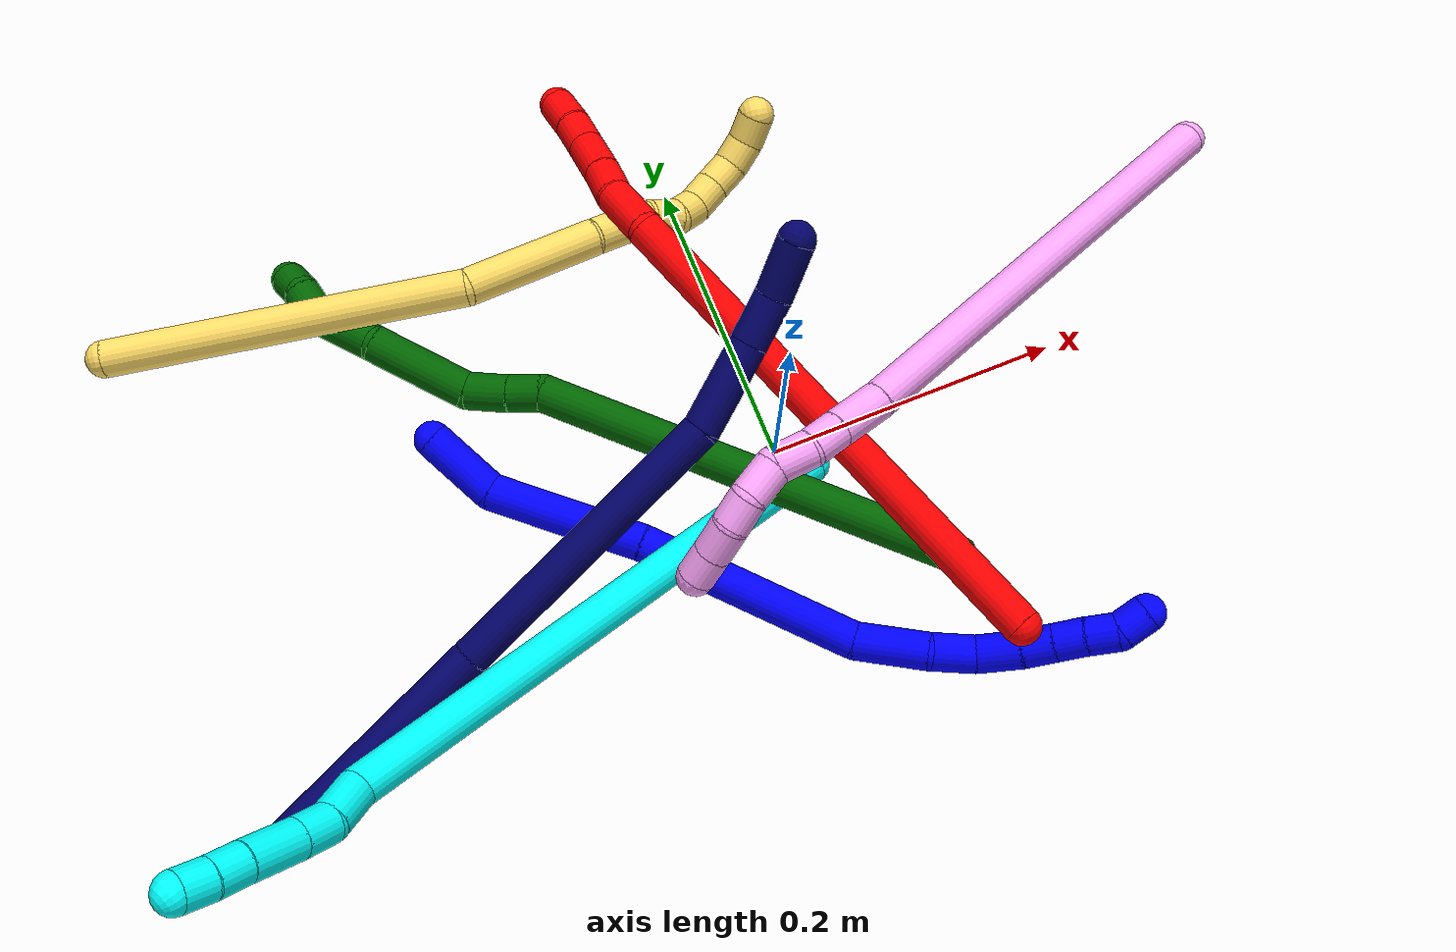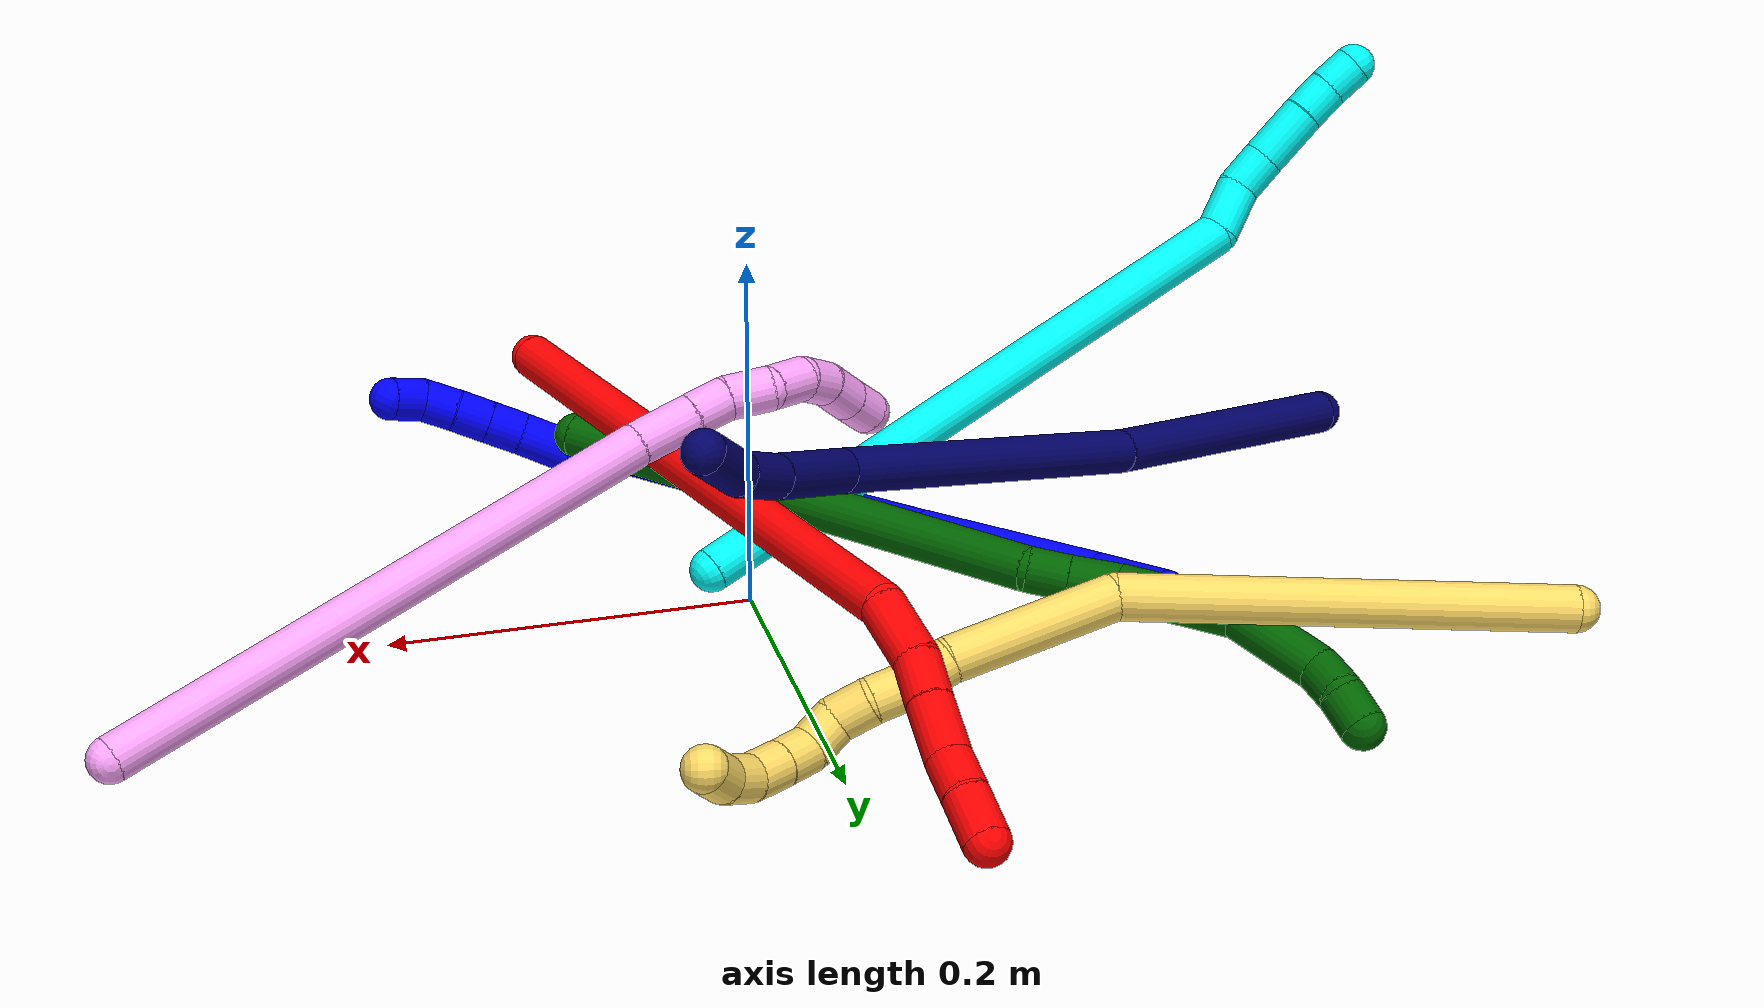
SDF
<sdf version="1.7">
 <world name="default">
  <plugin name="TubeGeneratorPlugin" filename="libtube_generator_plugin.so"/>
  <model name="photoneo_s_sensor">
   <static>1</static>
   <pose>0 0 2 1.57079 1.57079 3.14159</pose>
   <link name="link">
    <inertial><mass>0.1</mass></inertial>
    <sensor name="sensor" type="depth">
     <update_rate>30</update_rate>
     <camera>
      <horizontal_fov>1.22</horizontal_fov>
      <image><width>1920</width><height>1200</height><format>B8G8R8</format></image>
      <clip><near>0.1</near><far>4</far></clip>
      <depth_camera><output>points</output></depth_camera>
     </camera>
     <plugin name="camera_plugin" filename="libgazebo_ros_depth_camera.so">
      <baseline>0.2</baseline>
      <alwaysOn>1</alwaysOn>
      <updateRate>0.0</updateRate>
      <cameraName>camera_ir</cameraName>
      <imageTopicName>/camera/color/image_raw</imageTopicName>
      <cameraInfoTopicName>/camera/color/camera_info</cameraInfoTopicName>
      <depthImageTopicName>/camera/depth/image_raw</depthImageTopicName>
      <depthImageCameraInfoTopicName>/camera/depth/camera_info</depthImageCameraInfoTopicName>
      <pointCloudTopicName>/camera/depth/points</pointCloudTopicName>
      <frameName>fr_optical</frameName>
      <pointCloudCutoff>0.1</pointCloudCutoff>
      <pointCloudCutoffMax>2.0</pointCloudCutoffMax>
      <distortionK1>0</distortionK1>
      <distortionK2>0</distortionK2>
      <distortionK3>0</distortionK3>
      <distortionT1>0</distortionT1>
      <distortionT2>0</distortionT2>
      <CxPrime>0</CxPrime>
      <Cx>0</Cx>
      <Cy>0</Cy>
      <focalLength>0</focalLength>
      <hackBaseline>0</hackBaseline>
     </plugin>
    </sensor>
   </link>
  </model>
  <gravity>0 0 -9.8</gravity>
  <magnetic_field>6e-06 2.3e-05 -4.2e-05</magnetic_field>
  <atmosphere type="adiabatic"/>
  <physics name="default_physics" default="0" type="ode">
   <max_step_size>0.003</max_step_size>
   <real_time_factor>1</real_time_factor>
   <real_time_update_rate>1000</real_time_update_rate>
   <max_contacts>10000</max_contacts>
   <ode>
    <solver>
     <type>quick</type>
     <iters>100</iters>
     <sor>1.3</sor>
     <use_dynamic_moi_rescaling>0</use_dynamic_moi_rescaling>
    </solver>
    <constraints>
     <contact_max_correcting_vel>0</contact_max_correcting_vel>
     <contact_surface_layer>0.001</contact_surface_layer>
     <cfm>0</cfm>
     <erp>0.2</erp>
    </constraints>
   </ode>
  </physics>
  <scene><ambient>0.4 0.4 0.4 1</ambient><background>0.7 0.7 0.7 1</background><shadows>0</shadows></scene>
  <audio><device>default</device></audio>
  <spherical_coordinates>
   <surface_model>EARTH_WGS84</surface_model>
   <latitude_deg>0</latitude_deg>
   <longitude_deg>0</longitude_deg>
   <elevation>0</elevation>
   <heading_deg>0</heading_deg>
  </spherical_coordinates>
  <model name="bin">
   <static>1</static>
   <link name="bottom">
    <collision name="collision-bottom">
     <pose>0 0 -0.01 0 -0 0</pose>
     <geometry><box><size>0.8 0.6 0.02</size></box></geometry>
     <surface>
      <friction><ode><mu>100</mu><mu2>100</mu2></ode></friction>
      <contact><collide_bitmask>65535</collide_bitmask></contact>
     </surface>
    </collision>
   </link>
   <link name="west_wall">
    <collision name="collision-west_wall">
     <pose>-0.41 0 0.1 0 -0 0</pose>
     <geometry><box><size>0.02 0.6 0.2</size></box></geometry>
     <surface>
      <friction><ode><mu>100</mu><mu2>100</mu2></ode></friction>
      <contact><collide_bitmask>65535</collide_bitmask></contact>
     </surface>
    </collision>
   </link>
   <link name="east_wall">
    <collision name="collision-east_wall">
     <pose>0.41 0 0.1 0 -0 0</pose>
     <geometry><box><size>0.02 0.6 0.2</size></box></geometry>
     <surface>
      <friction><ode><mu>100</mu><mu2>100</mu2></ode></friction>
      <contact><collide_bitmask>65535</collide_bitmask></contact>
     </surface>
    </collision>
   </link>
   <link name="south_wall">
    <collision name="collision-south_wall">
     <pose>0 -0.31 0.1 0 -0 0</pose>
     <geometry><box><size>0.8 0.02 0.2</size></box></geometry>
     <surface>
      <friction><ode><mu>100</mu><mu2>100</mu2></ode></friction>
      <contact><collide_bitmask>65535</collide_bitmask></contact>
     </surface>
    </collision>
   </link>
   <link name="north_wall">
    <collision name="collision-north_wall">
     <pose>0 0.31 0.1 0 -0 0</pose>
     <geometry><box><size>0.8 0.02 0.2</size></box></geometry>
     <surface>
      <friction><ode><mu>100</mu><mu2>100</mu2></ode></friction>
      <contact><collide_bitmask>65535</collide_bitmask></contact>
     </surface>
    </collision>
   </link>
  </model>
  <model name="1">
   <static>0</static>
   <link name="1">
    <collision name="collision-cylinder-e_1_1_4">
     <pose>0.01701 -0.019149 -0.003366 1.7448 0.718748 0.841528</pose>
     <geometry><cylinder><radius>0.0125</radius><length>0.051667</length></cylinder></geometry>
     <surface>
      <friction><ode><mu>1.16</mu><mu2>1.16</mu2><slip1>0</slip1><slip2>0</slip2></ode></friction>
      <contact><ode><kp>1e+06</kp><kd>1</kd><max_vel>0</max_vel><min_depth>0.001</min_depth></ode></contact>
     </surface>
    </collision>
    <visual name="visual-cylinder-e_1_1_4">
     <pose>0.01701 -0.019149 -0.003366 1.7448 0.718748 0.841528</pose>
     <geometry><cylinder><radius>0.0125</radius><length>0.051667</length></cylinder></geometry>
     <material><ambient>0 0 1 1</ambient></material>
    </visual>
    <collision name="collision-cylinder-e_2_4_5">
     <pose>0.081727 -0.059724 -0.01683 2.01121 1.10998 1.54813</pose>
     <geometry><cylinder><radius>0.0125</radius><length>0.106526</length></cylinder></geometry>
     <surface>
      <friction><ode><mu>1.16</mu><mu2>1.16</mu2><slip1>0</slip1><slip2>0</slip2></ode></friction>
      <contact><ode><kp>1e+06</kp><kd>1</kd><max_vel>0</max_vel><min_depth>0.001</min_depth></ode></contact>
     </surface>
    </collision>
    <visual name="visual-cylinder-e_2_4_5">
     <pose>0.081727 -0.059724 -0.01683 2.01121 1.10998 1.54813</pose>
     <geometry><cylinder><radius>0.0125</radius><length>0.106526</length></cylinder></geometry>
     <material><ambient>0 0 1 1</ambient></material>
    </visual>
    <collision name="collision-cylinder-e_3_5_6">
     <pose>0.193707 -0.118707 -0.039444 1.8925 1.01873 1.31846</pose>
     <geometry><cylinder><radius>0.0125</radius><length>0.150975</length></cylinder></geometry>
     <surface>
      <friction><ode><mu>1.16</mu><mu2>1.16</mu2><slip1>0</slip1><slip2>0</slip2></ode></friction>
      <contact><ode><kp>1e+06</kp><kd>1</kd><max_vel>0</max_vel><min_depth>0.001</min_depth></ode></contact>
     </surface>
    </collision>
    <visual name="visual-cylinder-e_3_5_6">
     <pose>0.193707 -0.118707 -0.039444 1.8925 1.01873 1.31846</pose>
     <geometry><cylinder><radius>0.0125</radius><length>0.150975</length></cylinder></geometry>
     <material><ambient>0 0 1 1</ambient></material>
    </visual>
    <collision name="collision-cylinder-e_4_6_7">
     <pose>0.281345 -0.16134 -0.056178 2.26407 1.29556 2.03139</pose>
     <geometry><cylinder><radius>0.0125</radius><length>0.048556</length></cylinder></geometry>
     <surface>
      <friction><ode><mu>1.16</mu><mu2>1.16</mu2><slip1>0</slip1><slip2>0</slip2></ode></friction>
      <contact><ode><kp>1e+06</kp><kd>1</kd><max_vel>0</max_vel><min_depth>0.001</min_depth></ode></contact>
     </surface>
    </collision>
    <visual name="visual-cylinder-e_4_6_7">
     <pose>0.281345 -0.16134 -0.056178 2.26407 1.29556 2.03139</pose>
     <geometry><cylinder><radius>0.0125</radius><length>0.048556</length></cylinder></geometry>
     <material><ambient>0 0 1 1</ambient></material>
    </visual>
    <collision name="collision-cylinder-e_5_7_8">
     <pose>0.317841 -0.169555 -0.067158 2.70688 1.0544 2.41642</pose>
     <geometry><cylinder><radius>0.0125</radius><length>0.030202</length></cylinder></geometry>
     <surface>
      <friction><ode><mu>1.16</mu><mu2>1.16</mu2><slip1>0</slip1><slip2>0</slip2></ode></friction>
      <contact><ode><kp>1e+06</kp><kd>1</kd><max_vel>0</max_vel><min_depth>0.001</min_depth></ode></contact>
     </surface>
    </collision>
    <visual name="visual-cylinder-e_5_7_8">
     <pose>0.317841 -0.169555 -0.067158 2.70688 1.0544 2.41642</pose>
     <geometry><cylinder><radius>0.0125</radius><length>0.030202</length></cylinder></geometry>
     <material><ambient>0 0 1 1</ambient></material>
    </visual>
    <collision name="collision-cylinder-e_6_8_9">
     <pose>0.346425 -0.171371 -0.075116 -2.30519 1.45584 -2.2164</pose>
     <geometry><cylinder><radius>0.0125</radius><length>0.03111</length></cylinder></geometry>
     <surface>
      <friction><ode><mu>1.16</mu><mu2>1.16</mu2><slip1>0</slip1><slip2>0</slip2></ode></friction>
      <contact><ode><kp>1e+06</kp><kd>1</kd><max_vel>0</max_vel><min_depth>0.001</min_depth></ode></contact>
     </surface>
    </collision>
    <visual name="visual-cylinder-e_6_8_9">
     <pose>0.346425 -0.171371 -0.075116 -2.30519 1.45584 -2.2164</pose>
     <geometry><cylinder><radius>0.0125</radius><length>0.03111</length></cylinder></geometry>
     <material><ambient>0 0 1 1</ambient></material>
    </visual>
    <collision name="collision-cylinder-e_7_9_10">
     <pose>0.371973 -0.168266 -0.077401 -2.11961 1.36687 -1.9357</pose>
     <geometry><cylinder><radius>0.0125</radius><length>0.020618</length></cylinder></geometry>
     <surface>
      <friction><ode><mu>1.16</mu><mu2>1.16</mu2><slip1>0</slip1><slip2>0</slip2></ode></friction>
      <contact><ode><kp>1e+06</kp><kd>1</kd><max_vel>0</max_vel><min_depth>0.001</min_depth></ode></contact>
     </surface>
    </collision>
    <visual name="visual-cylinder-e_7_9_10">
     <pose>0.371973 -0.168266 -0.077401 -2.11961 1.36687 -1.9357</pose>
     <geometry><cylinder><radius>0.0125</radius><length>0.020618</length></cylinder></geometry>
     <material><ambient>0 0 1 1</ambient></material>
    </visual>
    <collision name="collision-cylinder-e_8_10_11">
     <pose>0.391878 -0.164801 -0.079536 -2.12679 1.37145 -1.94792</pose>
     <geometry><cylinder><radius>0.0125</radius><length>0.020016</length></cylinder></geometry>
     <surface>
      <friction><ode><mu>1.16</mu><mu2>1.16</mu2><slip1>0</slip1><slip2>0</slip2></ode></friction>
      <contact><ode><kp>1e+06</kp><kd>1</kd><max_vel>0</max_vel><min_depth>0.001</min_depth></ode></contact>
     </surface>
    </collision>
    <visual name="visual-cylinder-e_8_10_11">
     <pose>0.391878 -0.164801 -0.079536 -2.12679 1.37145 -1.94792</pose>
     <geometry><cylinder><radius>0.0125</radius><length>0.020016</length></cylinder></geometry>
     <material><ambient>0 0 1 1</ambient></material>
    </visual>
    <collision name="collision-cylinder-e_9_11_12">
     <pose>0.411681 -0.162085 -0.081971 -2.50228 1.39927 -2.3922</pose>
     <geometry><cylinder><radius>0.0125</radius><length>0.020282</length></cylinder></geometry>
     <surface>
      <friction><ode><mu>1.16</mu><mu2>1.16</mu2><slip1>0</slip1><slip2>0</slip2></ode></friction>
      <contact><ode><kp>1e+06</kp><kd>1</kd><max_vel>0</max_vel><min_depth>0.001</min_depth></ode></contact>
     </surface>
    </collision>
    <visual name="visual-cylinder-e_9_11_12">
     <pose>0.411681 -0.162085 -0.081971 -2.50228 1.39927 -2.3922</pose>
     <geometry><cylinder><radius>0.0125</radius><length>0.020282</length></cylinder></geometry>
     <material><ambient>0 0 1 1</ambient></material>
    </visual>
    <collision name="collision-cylinder-e_10_12_2">
     <pose>0.429653 -0.15624 -0.087052 -2.22527 0.920915 -1.57658</pose>
     <geometry><cylinder><radius>0.0125</radius><length>0.020047</length></cylinder></geometry>
     <surface>
      <friction><ode><mu>1.16</mu><mu2>1.16</mu2><slip1>0</slip1><slip2>0</slip2></ode></friction>
      <contact><ode><kp>1e+06</kp><kd>1</kd><max_vel>0</max_vel><min_depth>0.001</min_depth></ode></contact>
     </surface>
    </collision>
    <visual name="visual-cylinder-e_10_12_2">
     <pose>0.429653 -0.15624 -0.087052 -2.22527 0.920915 -1.57658</pose>
     <geometry><cylinder><radius>0.0125</radius><length>0.020047</length></cylinder></geometry>
     <material><ambient>0 0 1 1</ambient></material>
    </visual>
    <collision name="collision-sphere-2">
     <pose>0.437634 -0.151428 -0.090744 0 -0 0</pose>
     <geometry><sphere><radius>0.0125</radius></sphere></geometry>
     <surface>
      <friction><ode><mu>1.16</mu><mu2>1.16</mu2><slip1>0</slip1><slip2>0</slip2></ode></friction>
      <contact><ode><kp>1e+06</kp><kd>1</kd><max_vel>0</max_vel><min_depth>0.001</min_depth></ode></contact>
     </surface>
    </collision>
    <visual name="visual-sphere-2">
     <pose>0.437634 -0.151428 -0.090744 0 -0 0</pose>
     <geometry><sphere><radius>0.0125</radius></sphere></geometry>
     <material><ambient>0 0 1 1</ambient></material>
    </visual>
    <collision name="collision-sphere-12">
     <pose>0.421673 -0.161052 -0.08336 0 -0 0</pose>
     <geometry><sphere><radius>0.0125</radius></sphere></geometry>
     <surface>
      <friction><ode><mu>1.16</mu><mu2>1.16</mu2><slip1>0</slip1><slip2>0</slip2></ode></friction>
      <contact><ode><kp>1e+06</kp><kd>1</kd><max_vel>0</max_vel><min_depth>0.001</min_depth></ode></contact>
     </surface>
    </collision>
    <visual name="visual-sphere-12">
     <pose>0.421673 -0.161052 -0.08336 0 -0 0</pose>
     <geometry><sphere><radius>0.0125</radius></sphere></geometry>
     <material><ambient>0 0 1 1</ambient></material>
    </visual>
    <collision name="collision-sphere-11">
     <pose>0.401688 -0.163118 -0.080582 0 -0 0</pose>
     <geometry><sphere><radius>0.0125</radius></sphere></geometry>
     <surface>
      <friction><ode><mu>1.16</mu><mu2>1.16</mu2><slip1>0</slip1><slip2>0</slip2></ode></friction>
      <contact><ode><kp>1e+06</kp><kd>1</kd><max_vel>0</max_vel><min_depth>0.001</min_depth></ode></contact>
     </surface>
    </collision>
    <visual name="visual-sphere-11">
     <pose>0.401688 -0.163118 -0.080582 0 -0 0</pose>
     <geometry><sphere><radius>0.0125</radius></sphere></geometry>
     <material><ambient>0 0 1 1</ambient></material>
    </visual>
    <collision name="collision-sphere-10">
     <pose>0.382069 -0.166484 -0.07849 0 -0 0</pose>
     <geometry><sphere><radius>0.0125</radius></sphere></geometry>
     <surface>
      <friction><ode><mu>1.16</mu><mu2>1.16</mu2><slip1>0</slip1><slip2>0</slip2></ode></friction>
      <contact><ode><kp>1e+06</kp><kd>1</kd><max_vel>0</max_vel><min_depth>0.001</min_depth></ode></contact>
     </surface>
    </collision>
    <visual name="visual-sphere-10">
     <pose>0.382069 -0.166484 -0.07849 0 -0 0</pose>
     <geometry><sphere><radius>0.0125</radius></sphere></geometry>
     <material><ambient>0 0 1 1</ambient></material>
    </visual>
    <collision name="collision-sphere-9">
     <pose>0.361877 -0.170047 -0.076312 0 -0 0</pose>
     <geometry><sphere><radius>0.0125</radius></sphere></geometry>
     <surface>
      <friction><ode><mu>1.16</mu><mu2>1.16</mu2><slip1>0</slip1><slip2>0</slip2></ode></friction>
      <contact><ode><kp>1e+06</kp><kd>1</kd><max_vel>0</max_vel><min_depth>0.001</min_depth></ode></contact>
     </surface>
    </collision>
    <visual name="visual-sphere-9">
     <pose>0.361877 -0.170047 -0.076312 0 -0 0</pose>
     <geometry><sphere><radius>0.0125</radius></sphere></geometry>
     <material><ambient>0 0 1 1</ambient></material>
    </visual>
    <collision name="collision-sphere-4">
     <pose>0.03402 -0.038299 -0.006732 0 -0 0</pose>
     <geometry><sphere><radius>0.0125</radius></sphere></geometry>
     <surface>
      <friction><ode><mu>1.16</mu><mu2>1.16</mu2><slip1>0</slip1><slip2>0</slip2></ode></friction>
      <contact><ode><kp>1e+06</kp><kd>1</kd><max_vel>0</max_vel><min_depth>0.001</min_depth></ode></contact>
     </surface>
    </collision>
    <visual name="visual-sphere-4">
     <pose>0.03402 -0.038299 -0.006732 0 -0 0</pose>
     <geometry><sphere><radius>0.0125</radius></sphere></geometry>
     <material><ambient>0 0 1 1</ambient></material>
    </visual>
    <collision name="collision-sphere-1">
     <geometry><sphere><radius>0.0125</radius></sphere></geometry>
     <surface>
      <friction><ode><mu>1.16</mu><mu2>1.16</mu2><slip1>0</slip1><slip2>0</slip2></ode></friction>
      <contact><ode><kp>1e+06</kp><kd>1</kd><max_vel>0</max_vel><min_depth>0.001</min_depth></ode></contact>
     </surface>
    </collision>
    <visual name="visual-sphere-1">
     <geometry><sphere><radius>0.0125</radius></sphere></geometry>
     <material><ambient>0 0 1 1</ambient></material>
    </visual>
    <collision name="collision-sphere-8">
     <pose>0.330973 -0.172695 -0.07392 0 -0 0</pose>
     <geometry><sphere><radius>0.0125</radius></sphere></geometry>
     <surface>
      <friction><ode><mu>1.16</mu><mu2>1.16</mu2><slip1>0</slip1><slip2>0</slip2></ode></friction>
      <contact><ode><kp>1e+06</kp><kd>1</kd><max_vel>0</max_vel><min_depth>0.001</min_depth></ode></contact>
     </surface>
    </collision>
    <visual name="visual-sphere-8">
     <pose>0.330973 -0.172695 -0.07392 0 -0 0</pose>
     <geometry><sphere><radius>0.0125</radius></sphere></geometry>
     <material><ambient>0 0 1 1</ambient></material>
    </visual>
    <collision name="collision-sphere-5">
     <pose>0.129434 -0.081148 -0.026927 0 -0 0</pose>
     <geometry><sphere><radius>0.0125</radius></sphere></geometry>
     <surface>
      <friction><ode><mu>1.16</mu><mu2>1.16</mu2><slip1>0</slip1><slip2>0</slip2></ode></friction>
      <contact><ode><kp>1e+06</kp><kd>1</kd><max_vel>0</max_vel><min_depth>0.001</min_depth></ode></contact>
     </surface>
    </collision>
    <visual name="visual-sphere-5">
     <pose>0.129434 -0.081148 -0.026927 0 -0 0</pose>
     <geometry><sphere><radius>0.0125</radius></sphere></geometry>
     <material><ambient>0 0 1 1</ambient></material>
    </visual>
    <collision name="collision-sphere-6">
     <pose>0.25798 -0.156265 -0.051962 0 -0 0</pose>
     <geometry><sphere><radius>0.0125</radius></sphere></geometry>
     <surface>
      <friction><ode><mu>1.16</mu><mu2>1.16</mu2><slip1>0</slip1><slip2>0</slip2></ode></friction>
      <contact><ode><kp>1e+06</kp><kd>1</kd><max_vel>0</max_vel><min_depth>0.001</min_depth></ode></contact>
     </surface>
    </collision>
    <visual name="visual-sphere-6">
     <pose>0.25798 -0.156265 -0.051962 0 -0 0</pose>
     <geometry><sphere><radius>0.0125</radius></sphere></geometry>
     <material><ambient>0 0 1 1</ambient></material>
    </visual>
    <collision name="collision-sphere-7">
     <pose>0.304709 -0.166415 -0.060395 0 -0 0</pose>
     <geometry><sphere><radius>0.0125</radius></sphere></geometry>
     <surface>
      <friction><ode><mu>1.16</mu><mu2>1.16</mu2><slip1>0</slip1><slip2>0</slip2></ode></friction>
      <contact><ode><kp>1e+06</kp><kd>1</kd><max_vel>0</max_vel><min_depth>0.001</min_depth></ode></contact>
     </surface>
    </collision>
    <visual name="visual-sphere-7">
     <pose>0.304709 -0.166415 -0.060395 0 -0 0</pose>
     <geometry><sphere><radius>0.0125</radius></sphere></geometry>
     <material><ambient>0 0 1 1</ambient></material>
    </visual>
    <inertial>
     <pose>0.210688 -0.113494 -0.043221 0 -0 0</pose>
     <mass>0.5</mass>
     <inertia>
      <ixx>0.000282</ixx>
      <ixy>0</ixy>
      <ixz>0</ixz>
      <iyy>0.000511</iyy>
      <iyz>0</iyz>
      <izz>-0.000183</izz>
     </inertia>
    </inertial>
   </link>
   <pose>-0.20931 0.086832 0.020772 0.502986 -0.406361 -0.455154</pose>
  </model>
  <model name="2">
   <static>0</static>
   <link name="2">
    <collision name="collision-cylinder-e_1_1_4">
     <pose>-0.042637 0.131078 0.108665 -0.878614 -0.245373 0.115762</pose>
     <geometry><cylinder><radius>0.0125</radius><length>0.351042</length></cylinder></geometry>
     <surface>
      <friction><ode><mu>1.16</mu><mu2>1.16</mu2><slip1>0</slip1><slip2>0</slip2></ode></friction>
      <contact><ode><kp>1e+06</kp><kd>1</kd><max_vel>0</max_vel><min_depth>0.001</min_depth></ode></contact>
     </surface>
    </collision>
    <visual name="visual-cylinder-e_1_1_4">
     <pose>-0.042637 0.131078 0.108665 -0.878614 -0.245373 0.115762</pose>
     <geometry><cylinder><radius>0.0125</radius><length>0.351042</length></cylinder></geometry>
     <material><ambient>1 0 0 1</ambient></material>
    </visual>
    <collision name="collision-cylinder-e_2_4_5">
     <pose>-0.087917 0.280091 0.223551 -1.23693 -0.138312 0.0985</pose>
     <geometry><cylinder><radius>0.0125</radius><length>0.038331</length></cylinder></geometry>
     <surface>
      <friction><ode><mu>1.16</mu><mu2>1.16</mu2><slip1>0</slip1><slip2>0</slip2></ode></friction>
      <contact><ode><kp>1e+06</kp><kd>1</kd><max_vel>0</max_vel><min_depth>0.001</min_depth></ode></contact>
     </surface>
    </collision>
    <visual name="visual-cylinder-e_2_4_5">
     <pose>-0.087917 0.280091 0.223551 -1.23693 -0.138312 0.0985</pose>
     <geometry><cylinder><radius>0.0125</radius><length>0.038331</length></cylinder></geometry>
     <material><ambient>1 0 0 1</ambient></material>
    </visual>
    <collision name="collision-cylinder-e_3_5_6">
     <pose>-0.089574 0.310755 0.232986 -1.32349 0.07487 -0.058327</pose>
     <geometry><cylinder><radius>0.0125</radius><length>0.026332</length></cylinder></geometry>
     <surface>
      <friction><ode><mu>1.16</mu><mu2>1.16</mu2><slip1>0</slip1><slip2>0</slip2></ode></friction>
      <contact><ode><kp>1e+06</kp><kd>1</kd><max_vel>0</max_vel><min_depth>0.001</min_depth></ode></contact>
     </surface>
    </collision>
    <visual name="visual-cylinder-e_3_5_6">
     <pose>-0.089574 0.310755 0.232986 -1.32349 0.07487 -0.058327</pose>
     <geometry><cylinder><radius>0.0125</radius><length>0.026332</length></cylinder></geometry>
     <material><ambient>1 0 0 1</ambient></material>
    </visual>
    <collision name="collision-cylinder-e_4_6_7">
     <pose>-0.08808 0.339709 0.239796 -1.35269 0.030663 -0.024612</pose>
     <geometry><cylinder><radius>0.0125</radius><length>0.033252</length></cylinder></geometry>
     <surface>
      <friction><ode><mu>1.16</mu><mu2>1.16</mu2><slip1>0</slip1><slip2>0</slip2></ode></friction>
      <contact><ode><kp>1e+06</kp><kd>1</kd><max_vel>0</max_vel><min_depth>0.001</min_depth></ode></contact>
     </surface>
    </collision>
    <visual name="visual-cylinder-e_4_6_7">
     <pose>-0.08808 0.339709 0.239796 -1.35269 0.030663 -0.024612</pose>
     <geometry><cylinder><radius>0.0125</radius><length>0.033252</length></cylinder></geometry>
     <material><ambient>1 0 0 1</ambient></material>
    </visual>
    <collision name="collision-cylinder-e_5_7_8">
     <pose>-0.087529 0.366818 0.247785 -1.18715 0.003515 -0.002372</pose>
     <geometry><cylinder><radius>0.0125</radius><length>0.023475</length></cylinder></geometry>
     <surface>
      <friction><ode><mu>1.16</mu><mu2>1.16</mu2><slip1>0</slip1><slip2>0</slip2></ode></friction>
      <contact><ode><kp>1e+06</kp><kd>1</kd><max_vel>0</max_vel><min_depth>0.001</min_depth></ode></contact>
     </surface>
    </collision>
    <visual name="visual-cylinder-e_5_7_8">
     <pose>-0.087529 0.366818 0.247785 -1.18715 0.003515 -0.002372</pose>
     <geometry><cylinder><radius>0.0125</radius><length>0.023475</length></cylinder></geometry>
     <material><ambient>1 0 0 1</ambient></material>
    </visual>
    <collision name="collision-cylinder-e_6_8_2">
     <pose>-0.088092 0.391014 0.255703 -1.31193 -0.043882 0.033776</pose>
     <geometry><cylinder><radius>0.0125</radius><length>0.027568</length></cylinder></geometry>
     <surface>
      <friction><ode><mu>1.16</mu><mu2>1.16</mu2><slip1>0</slip1><slip2>0</slip2></ode></friction>
      <contact><ode><kp>1e+06</kp><kd>1</kd><max_vel>0</max_vel><min_depth>0.001</min_depth></ode></contact>
     </surface>
    </collision>
    <visual name="visual-cylinder-e_6_8_2">
     <pose>-0.088092 0.391014 0.255703 -1.31193 -0.043882 0.033776</pose>
     <geometry><cylinder><radius>0.0125</radius><length>0.027568</length></cylinder></geometry>
     <material><ambient>1 0 0 1</ambient></material>
    </visual>
    <collision name="collision-sphere-2">
     <pose>-0.088697 0.404326 0.259228 0 -0 0</pose>
     <geometry><sphere><radius>0.0125</radius></sphere></geometry>
     <surface>
      <friction><ode><mu>1.16</mu><mu2>1.16</mu2><slip1>0</slip1><slip2>0</slip2></ode></friction>
      <contact><ode><kp>1e+06</kp><kd>1</kd><max_vel>0</max_vel><min_depth>0.001</min_depth></ode></contact>
     </surface>
    </collision>
    <visual name="visual-sphere-2">
     <pose>-0.088697 0.404326 0.259228 0 -0 0</pose>
     <geometry><sphere><radius>0.0125</radius></sphere></geometry>
     <material><ambient>1 0 0 1</ambient></material>
    </visual>
    <collision name="collision-sphere-4">
     <pose>-0.085275 0.262157 0.217331 0 -0 0</pose>
     <geometry><sphere><radius>0.0125</radius></sphere></geometry>
     <surface>
      <friction><ode><mu>1.16</mu><mu2>1.16</mu2><slip1>0</slip1><slip2>0</slip2></ode></friction>
      <contact><ode><kp>1e+06</kp><kd>1</kd><max_vel>0</max_vel><min_depth>0.001</min_depth></ode></contact>
     </surface>
    </collision>
    <visual name="visual-sphere-4">
     <pose>-0.085275 0.262157 0.217331 0 -0 0</pose>
     <geometry><sphere><radius>0.0125</radius></sphere></geometry>
     <material><ambient>1 0 0 1</ambient></material>
    </visual>
    <collision name="collision-sphere-1">
     <geometry><sphere><radius>0.0125</radius></sphere></geometry>
     <surface>
      <friction><ode><mu>1.16</mu><mu2>1.16</mu2><slip1>0</slip1><slip2>0</slip2></ode></friction>
      <contact><ode><kp>1e+06</kp><kd>1</kd><max_vel>0</max_vel><min_depth>0.001</min_depth></ode></contact>
     </surface>
    </collision>
    <visual name="visual-sphere-1">
     <geometry><sphere><radius>0.0125</radius></sphere></geometry>
     <material><ambient>1 0 0 1</ambient></material>
    </visual>
    <collision name="collision-sphere-8">
     <pose>-0.087488 0.377702 0.252178 0 -0 0</pose>
     <geometry><sphere><radius>0.0125</radius></sphere></geometry>
     <surface>
      <friction><ode><mu>1.16</mu><mu2>1.16</mu2><slip1>0</slip1><slip2>0</slip2></ode></friction>
      <contact><ode><kp>1e+06</kp><kd>1</kd><max_vel>0</max_vel><min_depth>0.001</min_depth></ode></contact>
     </surface>
    </collision>
    <visual name="visual-sphere-8">
     <pose>-0.087488 0.377702 0.252178 0 -0 0</pose>
     <geometry><sphere><radius>0.0125</radius></sphere></geometry>
     <material><ambient>1 0 0 1</ambient></material>
    </visual>
    <collision name="collision-sphere-5">
     <pose>-0.090559 0.298026 0.229772 0 -0 0</pose>
     <geometry><sphere><radius>0.0125</radius></sphere></geometry>
     <surface>
      <friction><ode><mu>1.16</mu><mu2>1.16</mu2><slip1>0</slip1><slip2>0</slip2></ode></friction>
      <contact><ode><kp>1e+06</kp><kd>1</kd><max_vel>0</max_vel><min_depth>0.001</min_depth></ode></contact>
     </surface>
    </collision>
    <visual name="visual-sphere-5">
     <pose>-0.090559 0.298026 0.229772 0 -0 0</pose>
     <geometry><sphere><radius>0.0125</radius></sphere></geometry>
     <material><ambient>1 0 0 1</ambient></material>
    </visual>
    <collision name="collision-sphere-6">
     <pose>-0.08859 0.323485 0.2362 0 -0 0</pose>
     <geometry><sphere><radius>0.0125</radius></sphere></geometry>
     <surface>
      <friction><ode><mu>1.16</mu><mu2>1.16</mu2><slip1>0</slip1><slip2>0</slip2></ode></friction>
      <contact><ode><kp>1e+06</kp><kd>1</kd><max_vel>0</max_vel><min_depth>0.001</min_depth></ode></contact>
     </surface>
    </collision>
    <visual name="visual-sphere-6">
     <pose>-0.08859 0.323485 0.2362 0 -0 0</pose>
     <geometry><sphere><radius>0.0125</radius></sphere></geometry>
     <material><ambient>1 0 0 1</ambient></material>
    </visual>
    <collision name="collision-sphere-7">
     <pose>-0.08757 0.355934 0.243392 0 -0 0</pose>
     <geometry><sphere><radius>0.0125</radius></sphere></geometry>
     <surface>
      <friction><ode><mu>1.16</mu><mu2>1.16</mu2><slip1>0</slip1><slip2>0</slip2></ode></friction>
      <contact><ode><kp>1e+06</kp><kd>1</kd><max_vel>0</max_vel><min_depth>0.001</min_depth></ode></contact>
     </surface>
    </collision>
    <visual name="visual-sphere-7">
     <pose>-0.08757 0.355934 0.243392 0 -0 0</pose>
     <geometry><sphere><radius>0.0125</radius></sphere></geometry>
     <material><ambient>1 0 0 1</ambient></material>
    </visual>
    <inertial>
     <pose>-0.056216 0.191239 0.147379 0 -0 0</pose>
     <mass>0.5</mass>
     <inertia>
      <ixx>0.003904</ixx>
      <ixy>0</ixy>
      <ixz>0</ixz>
      <iyy>0.002815</iyy>
      <iyz>0</iyz>
      <izz>-0.00182</izz>
     </inertia>
    </inertial>
   </link>
   <pose>0.085203 -0.177345 0.079597 -0.705389 -0.025949 0.093864</pose>
  </model>
  <model name="3">
   <static>0</static>
   <link name="3">
    <collision name="collision-cylinder-e_1_1_4">
     <pose>-0.013847 -0.007737 0.183865 0.042053 -0.075104 -0.00158</pose>
     <geometry><cylinder><radius>0.0125</radius><length>0.369095</length></cylinder></geometry>
     <surface>
      <friction><ode><mu>1.16</mu><mu2>1.16</mu2><slip1>0</slip1><slip2>0</slip2></ode></friction>
      <contact><ode><kp>1e+06</kp><kd>1</kd><max_vel>0</max_vel><min_depth>0.001</min_depth></ode></contact>
     </surface>
    </collision>
    <visual name="visual-cylinder-e_1_1_4">
     <pose>-0.013847 -0.007737 0.183865 0.042053 -0.075104 -0.00158</pose>
     <geometry><cylinder><radius>0.0125</radius><length>0.369095</length></cylinder></geometry>
     <material><ambient>0.003922 1 0.996078 1</ambient></material>
    </visual>
    <collision name="collision-cylinder-e_2_4_5">
     <pose>-0.03306 -0.009807 0.381199 -0.39818 -0.351883 0.071708</pose>
     <geometry><cylinder><radius>0.0125</radius><length>0.031133</length></cylinder></geometry>
     <surface>
      <friction><ode><mu>1.16</mu><mu2>1.16</mu2><slip1>0</slip1><slip2>0</slip2></ode></friction>
      <contact><ode><kp>1e+06</kp><kd>1</kd><max_vel>0</max_vel><min_depth>0.001</min_depth></ode></contact>
     </surface>
    </collision>
    <visual name="visual-cylinder-e_2_4_5">
     <pose>-0.03306 -0.009807 0.381199 -0.39818 -0.351883 0.071708</pose>
     <geometry><cylinder><radius>0.0125</radius><length>0.031133</length></cylinder></geometry>
     <material><ambient>0.003922 1 0.996078 1</ambient></material>
    </visual>
    <collision name="collision-cylinder-e_3_5_6">
     <pose>-0.043669 -0.003716 0.405083 -0.040859 -0.466083 0.009699</pose>
     <geometry><cylinder><radius>0.0125</radius><length>0.023337</length></cylinder></geometry>
     <surface>
      <friction><ode><mu>1.16</mu><mu2>1.16</mu2><slip1>0</slip1><slip2>0</slip2></ode></friction>
      <contact><ode><kp>1e+06</kp><kd>1</kd><max_vel>0</max_vel><min_depth>0.001</min_depth></ode></contact>
     </surface>
    </collision>
    <visual name="visual-cylinder-e_3_5_6">
     <pose>-0.043669 -0.003716 0.405083 -0.040859 -0.466083 0.009699</pose>
     <geometry><cylinder><radius>0.0125</radius><length>0.023337</length></cylinder></geometry>
     <material><ambient>0.003922 1 0.996078 1</ambient></material>
    </visual>
    <collision name="collision-cylinder-e_4_6_7">
     <pose>-0.057276 -0.003283 0.431039 -0.000457 -0.493732 0.000115</pose>
     <geometry><cylinder><radius>0.0125</radius><length>0.035296</length></cylinder></geometry>
     <surface>
      <friction><ode><mu>1.16</mu><mu2>1.16</mu2><slip1>0</slip1><slip2>0</slip2></ode></friction>
      <contact><ode><kp>1e+06</kp><kd>1</kd><max_vel>0</max_vel><min_depth>0.001</min_depth></ode></contact>
     </surface>
    </collision>
    <visual name="visual-cylinder-e_4_6_7">
     <pose>-0.057276 -0.003283 0.431039 -0.000457 -0.493732 0.000115</pose>
     <geometry><cylinder><radius>0.0125</radius><length>0.035296</length></cylinder></geometry>
     <material><ambient>0.003922 1 0.996078 1</ambient></material>
    </visual>
    <collision name="collision-cylinder-e_5_7_8">
     <pose>-0.070094 -0.003364 0.456113 0.009232 -0.437097 -0.00205</pose>
     <geometry><cylinder><radius>0.0125</radius><length>0.021045</length></cylinder></geometry>
     <surface>
      <friction><ode><mu>1.16</mu><mu2>1.16</mu2><slip1>0</slip1><slip2>0</slip2></ode></friction>
      <contact><ode><kp>1e+06</kp><kd>1</kd><max_vel>0</max_vel><min_depth>0.001</min_depth></ode></contact>
     </surface>
    </collision>
    <visual name="visual-cylinder-e_5_7_8">
     <pose>-0.070094 -0.003364 0.456113 0.009232 -0.437097 -0.00205</pose>
     <geometry><cylinder><radius>0.0125</radius><length>0.021045</length></cylinder></geometry>
     <material><ambient>0.003922 1 0.996078 1</ambient></material>
    </visual>
    <collision name="collision-cylinder-e_6_8_2">
     <pose>-0.078761 -0.004381 0.474719 0.102077 -0.432643 -0.022451</pose>
     <geometry><cylinder><radius>0.0125</radius><length>0.020093</length></cylinder></geometry>
     <surface>
      <friction><ode><mu>1.16</mu><mu2>1.16</mu2><slip1>0</slip1><slip2>0</slip2></ode></friction>
      <contact><ode><kp>1e+06</kp><kd>1</kd><max_vel>0</max_vel><min_depth>0.001</min_depth></ode></contact>
     </surface>
    </collision>
    <visual name="visual-cylinder-e_6_8_2">
     <pose>-0.078761 -0.004381 0.474719 0.102077 -0.432643 -0.022451</pose>
     <geometry><cylinder><radius>0.0125</radius><length>0.020093</length></cylinder></geometry>
     <material><ambient>0.003922 1 0.996078 1</ambient></material>
    </visual>
    <collision name="collision-sphere-2">
     <pose>-0.082973 -0.00531 0.483792 0 -0 0</pose>
     <geometry><sphere><radius>0.0125</radius></sphere></geometry>
     <surface>
      <friction><ode><mu>1.16</mu><mu2>1.16</mu2><slip1>0</slip1><slip2>0</slip2></ode></friction>
      <contact><ode><kp>1e+06</kp><kd>1</kd><max_vel>0</max_vel><min_depth>0.001</min_depth></ode></contact>
     </surface>
    </collision>
    <visual name="visual-sphere-2">
     <pose>-0.082973 -0.00531 0.483792 0 -0 0</pose>
     <geometry><sphere><radius>0.0125</radius></sphere></geometry>
     <material><ambient>0.003922 1 0.996078 1</ambient></material>
    </visual>
    <collision name="collision-sphere-4">
     <pose>-0.027695 -0.015473 0.367729 0 -0 0</pose>
     <geometry><sphere><radius>0.0125</radius></sphere></geometry>
     <surface>
      <friction><ode><mu>1.16</mu><mu2>1.16</mu2><slip1>0</slip1><slip2>0</slip2></ode></friction>
      <contact><ode><kp>1e+06</kp><kd>1</kd><max_vel>0</max_vel><min_depth>0.001</min_depth></ode></contact>
     </surface>
    </collision>
    <visual name="visual-sphere-4">
     <pose>-0.027695 -0.015473 0.367729 0 -0 0</pose>
     <geometry><sphere><radius>0.0125</radius></sphere></geometry>
     <material><ambient>0.003922 1 0.996078 1</ambient></material>
    </visual>
    <collision name="collision-sphere-1">
     <geometry><sphere><radius>0.0125</radius></sphere></geometry>
     <surface>
      <friction><ode><mu>1.16</mu><mu2>1.16</mu2><slip1>0</slip1><slip2>0</slip2></ode></friction>
      <contact><ode><kp>1e+06</kp><kd>1</kd><max_vel>0</max_vel><min_depth>0.001</min_depth></ode></contact>
     </surface>
    </collision>
    <visual name="visual-sphere-1">
     <geometry><sphere><radius>0.0125</radius></sphere></geometry>
     <material><ambient>0.003922 1 0.996078 1</ambient></material>
    </visual>
    <collision name="collision-sphere-8">
     <pose>-0.074549 -0.003452 0.465646 0 -0 0</pose>
     <geometry><sphere><radius>0.0125</radius></sphere></geometry>
     <surface>
      <friction><ode><mu>1.16</mu><mu2>1.16</mu2><slip1>0</slip1><slip2>0</slip2></ode></friction>
      <contact><ode><kp>1e+06</kp><kd>1</kd><max_vel>0</max_vel><min_depth>0.001</min_depth></ode></contact>
     </surface>
    </collision>
    <visual name="visual-sphere-8">
     <pose>-0.074549 -0.003452 0.465646 0 -0 0</pose>
     <geometry><sphere><radius>0.0125</radius></sphere></geometry>
     <material><ambient>0.003922 1 0.996078 1</ambient></material>
    </visual>
    <collision name="collision-sphere-5">
     <pose>-0.038425 -0.004141 0.394668 0 -0 0</pose>
     <geometry><sphere><radius>0.0125</radius></sphere></geometry>
     <surface>
      <friction><ode><mu>1.16</mu><mu2>1.16</mu2><slip1>0</slip1><slip2>0</slip2></ode></friction>
      <contact><ode><kp>1e+06</kp><kd>1</kd><max_vel>0</max_vel><min_depth>0.001</min_depth></ode></contact>
     </surface>
    </collision>
    <visual name="visual-sphere-5">
     <pose>-0.038425 -0.004141 0.394668 0 -0 0</pose>
     <geometry><sphere><radius>0.0125</radius></sphere></geometry>
     <material><ambient>0.003922 1 0.996078 1</ambient></material>
    </visual>
    <collision name="collision-sphere-6">
     <pose>-0.048912 -0.00329 0.415499 0 -0 0</pose>
     <geometry><sphere><radius>0.0125</radius></sphere></geometry>
     <surface>
      <friction><ode><mu>1.16</mu><mu2>1.16</mu2><slip1>0</slip1><slip2>0</slip2></ode></friction>
      <contact><ode><kp>1e+06</kp><kd>1</kd><max_vel>0</max_vel><min_depth>0.001</min_depth></ode></contact>
     </surface>
    </collision>
    <visual name="visual-sphere-6">
     <pose>-0.048912 -0.00329 0.415499 0 -0 0</pose>
     <geometry><sphere><radius>0.0125</radius></sphere></geometry>
     <material><ambient>0.003922 1 0.996078 1</ambient></material>
    </visual>
    <collision name="collision-sphere-7">
     <pose>-0.06564 -0.003276 0.44658 0 -0 0</pose>
     <geometry><sphere><radius>0.0125</radius></sphere></geometry>
     <surface>
      <friction><ode><mu>1.16</mu><mu2>1.16</mu2><slip1>0</slip1><slip2>0</slip2></ode></friction>
      <contact><ode><kp>1e+06</kp><kd>1</kd><max_vel>0</max_vel><min_depth>0.001</min_depth></ode></contact>
     </surface>
    </collision>
    <visual name="visual-sphere-7">
     <pose>-0.06564 -0.003276 0.44658 0 -0 0</pose>
     <geometry><sphere><radius>0.0125</radius></sphere></geometry>
     <material><ambient>0.003922 1 0.996078 1</ambient></material>
    </visual>
    <inertial>
     <pose>-0.024477 -0.007045 0.247073 0 -0 0</pose>
     <mass>0.5</mass>
     <inertia>
      <ixx>0.004192</ixx>
      <ixy>0</ixy>
      <ixz>0</ixz>
      <iyy>0.004208</iyy>
      <iyz>0</iyz>
      <izz>0.000534</izz>
     </inertia>
    </inertial>
   </link>
   <pose>0.017108 -0.01964 0.011488 0.826712 1.15023 -1.88537</pose>
  </model>
  <model name="4">
   <static>0</static>
   <link name="4">
    <collision name="collision-cylinder-e_1_1_4">
     <pose>-0.156016 -0.025528 -0.043532 2.61122 -1.25796 -2.42706</pose>
     <geometry><cylinder><radius>0.0125</radius><length>0.32795</length></cylinder></geometry>
     <surface>
      <friction><ode><mu>1.16</mu><mu2>1.16</mu2><slip1>0</slip1><slip2>0</slip2></ode></friction>
      <contact><ode><kp>1e+06</kp><kd>1</kd><max_vel>0</max_vel><min_depth>0.001</min_depth></ode></contact>
     </surface>
    </collision>
    <visual name="visual-cylinder-e_1_1_4">
     <pose>-0.156016 -0.025528 -0.043532 2.61122 -1.25796 -2.42706</pose>
     <geometry><cylinder><radius>0.0125</radius><length>0.32795</length></cylinder></geometry>
     <material><ambient>1 0.65098 0.996078 1</ambient></material>
    </visual>
    <collision name="collision-cylinder-e_2_4_5">
     <pose>-0.329289 -0.053205 -0.090566 2.59124 -1.33706 -2.45499</pose>
     <geometry><cylinder><radius>0.0125</radius><length>0.035478</length></cylinder></geometry>
     <surface>
      <friction><ode><mu>1.16</mu><mu2>1.16</mu2><slip1>0</slip1><slip2>0</slip2></ode></friction>
      <contact><ode><kp>1e+06</kp><kd>1</kd><max_vel>0</max_vel><min_depth>0.001</min_depth></ode></contact>
     </surface>
    </collision>
    <visual name="visual-cylinder-e_2_4_5">
     <pose>-0.329289 -0.053205 -0.090566 2.59124 -1.33706 -2.45499</pose>
     <geometry><cylinder><radius>0.0125</radius><length>0.035478</length></cylinder></geometry>
     <material><ambient>1 0.65098 0.996078 1</ambient></material>
    </visual>
    <collision name="collision-cylinder-e_3_5_6">
     <pose>-0.357279 -0.056611 -0.096363 2.64033 -1.3317 -2.51147</pose>
     <geometry><cylinder><radius>0.0125</radius><length>0.022096</length></cylinder></geometry>
     <surface>
      <friction><ode><mu>1.16</mu><mu2>1.16</mu2><slip1>0</slip1><slip2>0</slip2></ode></friction>
      <contact><ode><kp>1e+06</kp><kd>1</kd><max_vel>0</max_vel><min_depth>0.001</min_depth></ode></contact>
     </surface>
    </collision>
    <visual name="visual-cylinder-e_3_5_6">
     <pose>-0.357279 -0.056611 -0.096363 2.64033 -1.3317 -2.51147</pose>
     <geometry><cylinder><radius>0.0125</radius><length>0.022096</length></cylinder></geometry>
     <material><ambient>1 0.65098 0.996078 1</ambient></material>
    </visual>
    <collision name="collision-cylinder-e_4_6_7">
     <pose>-0.380846 -0.05659 -0.099397 -2.09516 -1.45624 1.99305</pose>
     <geometry><cylinder><radius>0.0125</radius><length>0.025835</length></cylinder></geometry>
     <surface>
      <friction><ode><mu>1.16</mu><mu2>1.16</mu2><slip1>0</slip1><slip2>0</slip2></ode></friction>
      <contact><ode><kp>1e+06</kp><kd>1</kd><max_vel>0</max_vel><min_depth>0.001</min_depth></ode></contact>
     </surface>
    </collision>
    <visual name="visual-cylinder-e_4_6_7">
     <pose>-0.380846 -0.05659 -0.099397 -2.09516 -1.45624 1.99305</pose>
     <geometry><cylinder><radius>0.0125</radius><length>0.025835</length></cylinder></geometry>
     <material><ambient>1 0.65098 0.996078 1</ambient></material>
    </visual>
    <collision name="collision-cylinder-e_5_7_8">
     <pose>-0.404219 -0.053901 -0.106135 -2.91048 -1.0417 2.74233</pose>
     <geometry><cylinder><radius>0.0125</radius><length>0.024419</length></cylinder></geometry>
     <surface>
      <friction><ode><mu>1.16</mu><mu2>1.16</mu2><slip1>0</slip1><slip2>0</slip2></ode></friction>
      <contact><ode><kp>1e+06</kp><kd>1</kd><max_vel>0</max_vel><min_depth>0.001</min_depth></ode></contact>
     </surface>
    </collision>
    <visual name="visual-cylinder-e_5_7_8">
     <pose>-0.404219 -0.053901 -0.106135 -2.91048 -1.0417 2.74233</pose>
     <geometry><cylinder><radius>0.0125</radius><length>0.024419</length></cylinder></geometry>
     <material><ambient>1 0.65098 0.996078 1</ambient></material>
    </visual>
    <collision name="collision-cylinder-e_6_8_9">
     <pose>-0.421946 -0.047833 -0.118169 -2.48448 -0.756055 1.72283</pose>
     <geometry><cylinder><radius>0.0125</radius><length>0.020952</length></cylinder></geometry>
     <surface>
      <friction><ode><mu>1.16</mu><mu2>1.16</mu2><slip1>0</slip1><slip2>0</slip2></ode></friction>
      <contact><ode><kp>1e+06</kp><kd>1</kd><max_vel>0</max_vel><min_depth>0.001</min_depth></ode></contact>
     </surface>
    </collision>
    <visual name="visual-cylinder-e_6_8_9">
     <pose>-0.421946 -0.047833 -0.118169 -2.48448 -0.756055 1.72283</pose>
     <geometry><cylinder><radius>0.0125</radius><length>0.020952</length></cylinder></geometry>
     <material><ambient>1 0.65098 0.996078 1</ambient></material>
    </visual>
    <collision name="collision-cylinder-e_7_9_10">
     <pose>-0.435264 -0.035849 -0.130286 -2.26358 -0.571883 1.11879</pose>
     <geometry><cylinder><radius>0.0125</radius><length>0.022654</length></cylinder></geometry>
     <surface>
      <friction><ode><mu>1.16</mu><mu2>1.16</mu2><slip1>0</slip1><slip2>0</slip2></ode></friction>
      <contact><ode><kp>1e+06</kp><kd>1</kd><max_vel>0</max_vel><min_depth>0.001</min_depth></ode></contact>
     </surface>
    </collision>
    <visual name="visual-cylinder-e_7_9_10">
     <pose>-0.435264 -0.035849 -0.130286 -2.26358 -0.571883 1.11879</pose>
     <geometry><cylinder><radius>0.0125</radius><length>0.022654</length></cylinder></geometry>
     <material><ambient>1 0.65098 0.996078 1</ambient></material>
    </visual>
    <collision name="collision-cylinder-e_8_10_2">
     <pose>-0.44724 -0.021971 -0.141773 -2.26073 -0.603026 1.16655</pose>
     <geometry><cylinder><radius>0.0125</radius><length>0.020616</length></cylinder></geometry>
     <surface>
      <friction><ode><mu>1.16</mu><mu2>1.16</mu2><slip1>0</slip1><slip2>0</slip2></ode></friction>
      <contact><ode><kp>1e+06</kp><kd>1</kd><max_vel>0</max_vel><min_depth>0.001</min_depth></ode></contact>
     </surface>
    </collision>
    <visual name="visual-cylinder-e_8_10_2">
     <pose>-0.44724 -0.021971 -0.141773 -2.26073 -0.603026 1.16655</pose>
     <geometry><cylinder><radius>0.0125</radius><length>0.020616</length></cylinder></geometry>
     <material><ambient>1 0.65098 0.996078 1</ambient></material>
    </visual>
    <collision name="collision-sphere-2">
     <pose>-0.453086 -0.015423 -0.147177 0 -0 0</pose>
     <geometry><sphere><radius>0.0125</radius></sphere></geometry>
     <surface>
      <friction><ode><mu>1.16</mu><mu2>1.16</mu2><slip1>0</slip1><slip2>0</slip2></ode></friction>
      <contact><ode><kp>1e+06</kp><kd>1</kd><max_vel>0</max_vel><min_depth>0.001</min_depth></ode></contact>
     </surface>
    </collision>
    <visual name="visual-sphere-2">
     <pose>-0.453086 -0.015423 -0.147177 0 -0 0</pose>
     <geometry><sphere><radius>0.0125</radius></sphere></geometry>
     <material><ambient>1 0.65098 0.996078 1</ambient></material>
    </visual>
    <collision name="collision-sphere-10">
     <pose>-0.441394 -0.028519 -0.13637 0 -0 0</pose>
     <geometry><sphere><radius>0.0125</radius></sphere></geometry>
     <surface>
      <friction><ode><mu>1.16</mu><mu2>1.16</mu2><slip1>0</slip1><slip2>0</slip2></ode></friction>
      <contact><ode><kp>1e+06</kp><kd>1</kd><max_vel>0</max_vel><min_depth>0.001</min_depth></ode></contact>
     </surface>
    </collision>
    <visual name="visual-sphere-10">
     <pose>-0.441394 -0.028519 -0.13637 0 -0 0</pose>
     <geometry><sphere><radius>0.0125</radius></sphere></geometry>
     <material><ambient>1 0.65098 0.996078 1</ambient></material>
    </visual>
    <collision name="collision-sphere-9">
     <pose>-0.429133 -0.043178 -0.124203 0 -0 0</pose>
     <geometry><sphere><radius>0.0125</radius></sphere></geometry>
     <surface>
      <friction><ode><mu>1.16</mu><mu2>1.16</mu2><slip1>0</slip1><slip2>0</slip2></ode></friction>
      <contact><ode><kp>1e+06</kp><kd>1</kd><max_vel>0</max_vel><min_depth>0.001</min_depth></ode></contact>
     </surface>
    </collision>
    <visual name="visual-sphere-9">
     <pose>-0.429133 -0.043178 -0.124203 0 -0 0</pose>
     <geometry><sphere><radius>0.0125</radius></sphere></geometry>
     <material><ambient>1 0.65098 0.996078 1</ambient></material>
    </visual>
    <collision name="collision-sphere-4">
     <pose>-0.312033 -0.051056 -0.087064 0 -0 0</pose>
     <geometry><sphere><radius>0.0125</radius></sphere></geometry>
     <surface>
      <friction><ode><mu>1.16</mu><mu2>1.16</mu2><slip1>0</slip1><slip2>0</slip2></ode></friction>
      <contact><ode><kp>1e+06</kp><kd>1</kd><max_vel>0</max_vel><min_depth>0.001</min_depth></ode></contact>
     </surface>
    </collision>
    <visual name="visual-sphere-4">
     <pose>-0.312033 -0.051056 -0.087064 0 -0 0</pose>
     <geometry><sphere><radius>0.0125</radius></sphere></geometry>
     <material><ambient>1 0.65098 0.996078 1</ambient></material>
    </visual>
    <collision name="collision-sphere-1">
     <geometry><sphere><radius>0.0125</radius></sphere></geometry>
     <surface>
      <friction><ode><mu>1.16</mu><mu2>1.16</mu2><slip1>0</slip1><slip2>0</slip2></ode></friction>
      <contact><ode><kp>1e+06</kp><kd>1</kd><max_vel>0</max_vel><min_depth>0.001</min_depth></ode></contact>
     </surface>
    </collision>
    <visual name="visual-sphere-1">
     <geometry><sphere><radius>0.0125</radius></sphere></geometry>
     <material><ambient>1 0.65098 0.996078 1</ambient></material>
    </visual>
    <collision name="collision-sphere-8">
     <pose>-0.414759 -0.052489 -0.112134 0 -0 0</pose>
     <geometry><sphere><radius>0.0125</radius></sphere></geometry>
     <surface>
      <friction><ode><mu>1.16</mu><mu2>1.16</mu2><slip1>0</slip1><slip2>0</slip2></ode></friction>
      <contact><ode><kp>1e+06</kp><kd>1</kd><max_vel>0</max_vel><min_depth>0.001</min_depth></ode></contact>
     </surface>
    </collision>
    <visual name="visual-sphere-8">
     <pose>-0.414759 -0.052489 -0.112134 0 -0 0</pose>
     <geometry><sphere><radius>0.0125</radius></sphere></geometry>
     <material><ambient>1 0.65098 0.996078 1</ambient></material>
    </visual>
    <collision name="collision-sphere-5">
     <pose>-0.346546 -0.055354 -0.094068 0 -0 0</pose>
     <geometry><sphere><radius>0.0125</radius></sphere></geometry>
     <surface>
      <friction><ode><mu>1.16</mu><mu2>1.16</mu2><slip1>0</slip1><slip2>0</slip2></ode></friction>
      <contact><ode><kp>1e+06</kp><kd>1</kd><max_vel>0</max_vel><min_depth>0.001</min_depth></ode></contact>
     </surface>
    </collision>
    <visual name="visual-sphere-5">
     <pose>-0.346546 -0.055354 -0.094068 0 -0 0</pose>
     <geometry><sphere><radius>0.0125</radius></sphere></geometry>
     <material><ambient>1 0.65098 0.996078 1</ambient></material>
    </visual>
    <collision name="collision-sphere-6">
     <pose>-0.368013 -0.057868 -0.098657 0 -0 0</pose>
     <geometry><sphere><radius>0.0125</radius></sphere></geometry>
     <surface>
      <friction><ode><mu>1.16</mu><mu2>1.16</mu2><slip1>0</slip1><slip2>0</slip2></ode></friction>
      <contact><ode><kp>1e+06</kp><kd>1</kd><max_vel>0</max_vel><min_depth>0.001</min_depth></ode></contact>
     </surface>
    </collision>
    <visual name="visual-sphere-6">
     <pose>-0.368013 -0.057868 -0.098657 0 -0 0</pose>
     <geometry><sphere><radius>0.0125</radius></sphere></geometry>
     <material><ambient>1 0.65098 0.996078 1</ambient></material>
    </visual>
    <collision name="collision-sphere-7">
     <pose>-0.393679 -0.055312 -0.100136 0 -0 0</pose>
     <geometry><sphere><radius>0.0125</radius></sphere></geometry>
     <surface>
      <friction><ode><mu>1.16</mu><mu2>1.16</mu2><slip1>0</slip1><slip2>0</slip2></ode></friction>
      <contact><ode><kp>1e+06</kp><kd>1</kd><max_vel>0</max_vel><min_depth>0.001</min_depth></ode></contact>
     </surface>
    </collision>
    <visual name="visual-sphere-7">
     <pose>-0.393679 -0.055312 -0.100136 0 -0 0</pose>
     <geometry><sphere><radius>0.0125</radius></sphere></geometry>
     <material><ambient>1 0.65098 0.996078 1</ambient></material>
    </visual>
    <inertial>
     <pose>-0.236747 -0.033112 -0.066257 0 -0 0</pose>
     <mass>0.5</mass>
     <inertia>
      <ixx>-0.001315</ixx>
      <ixy>0</ixy>
      <ixz>0</ixz>
      <iyy>0.002274</iyy>
      <iyz>0</iyz>
      <izz>0.003268</izz>
     </inertia>
    </inertial>
   </link>
   <pose>0.353137 0.100624 0.011497 -1.27698 0.191898 0.064569</pose>
  </model>
  <model name="5">
   <static>0</static>
   <link name="5">
    <collision name="collision-cylinder-e_1_1_4">
     <pose>-0.003421 -0.005019 -0.120276 3.09989 -0.028407 -1.1959</pose>
     <geometry><cylinder><radius>0.0125</radius><length>0.240859</length></cylinder></geometry>
     <surface>
      <friction><ode><mu>1.16</mu><mu2>1.16</mu2><slip1>0</slip1><slip2>0</slip2></ode></friction>
      <contact><ode><kp>1e+06</kp><kd>1</kd><max_vel>0</max_vel><min_depth>0.001</min_depth></ode></contact>
     </surface>
    </collision>
    <visual name="visual-cylinder-e_1_1_4">
     <pose>-0.003421 -0.005019 -0.120276 3.09989 -0.028407 -1.1959</pose>
     <geometry><cylinder><radius>0.0125</radius><length>0.240859</length></cylinder></geometry>
     <material><ambient>1 0.858824 0.4 1</ambient></material>
    </visual>
    <collision name="collision-cylinder-e_2_4_5">
     <pose>0.007399 -0.002014 -0.284381 -2.96053 0.309334 -2.08708</pose>
     <geometry><cylinder><radius>0.0125</radius><length>0.093554</length></cylinder></geometry>
     <surface>
      <friction><ode><mu>1.16</mu><mu2>1.16</mu2><slip1>0</slip1><slip2>0</slip2></ode></friction>
      <contact><ode><kp>1e+06</kp><kd>1</kd><max_vel>0</max_vel><min_depth>0.001</min_depth></ode></contact>
     </surface>
    </collision>
    <visual name="visual-cylinder-e_2_4_5">
     <pose>0.007399 -0.002014 -0.284381 -2.96053 0.309334 -2.08708</pose>
     <geometry><cylinder><radius>0.0125</radius><length>0.093554</length></cylinder></geometry>
     <material><ambient>1 0.858824 0.4 1</ambient></material>
    </visual>
    <collision name="collision-cylinder-e_3_5_6">
     <pose>0.026116 0.01004 -0.338466 -2.76721 0.38592 -1.60188</pose>
     <geometry><cylinder><radius>0.0125</radius><length>0.02379</length></cylinder></geometry>
     <surface>
      <friction><ode><mu>1.16</mu><mu2>1.16</mu2><slip1>0</slip1><slip2>0</slip2></ode></friction>
      <contact><ode><kp>1e+06</kp><kd>1</kd><max_vel>0</max_vel><min_depth>0.001</min_depth></ode></contact>
     </surface>
    </collision>
    <visual name="visual-cylinder-e_3_5_6">
     <pose>0.026116 0.01004 -0.338466 -2.76721 0.38592 -1.60188</pose>
     <geometry><cylinder><radius>0.0125</radius><length>0.02379</length></cylinder></geometry>
     <material><ambient>1 0.858824 0.4 1</ambient></material>
    </visual>
    <collision name="collision-cylinder-e_4_6_7">
     <pose>0.033279 0.016634 -0.358548 -2.88631 0.258491 -1.58342</pose>
     <geometry><cylinder><radius>0.0125</radius><length>0.021006</length></cylinder></geometry>
     <surface>
      <friction><ode><mu>1.16</mu><mu2>1.16</mu2><slip1>0</slip1><slip2>0</slip2></ode></friction>
      <contact><ode><kp>1e+06</kp><kd>1</kd><max_vel>0</max_vel><min_depth>0.001</min_depth></ode></contact>
     </surface>
    </collision>
    <visual name="visual-cylinder-e_4_6_7">
     <pose>0.033279 0.016634 -0.358548 -2.88631 0.258491 -1.58342</pose>
     <geometry><cylinder><radius>0.0125</radius><length>0.021006</length></cylinder></geometry>
     <material><ambient>1 0.858824 0.4 1</ambient></material>
    </visual>
    <collision name="collision-cylinder-e_5_7_8">
     <pose>0.037202 0.024045 -0.377449 -2.65111 0.119761 -0.470218</pose>
     <geometry><cylinder><radius>0.0125</radius><length>0.020727</length></cylinder></geometry>
     <surface>
      <friction><ode><mu>1.16</mu><mu2>1.16</mu2><slip1>0</slip1><slip2>0</slip2></ode></friction>
      <contact><ode><kp>1e+06</kp><kd>1</kd><max_vel>0</max_vel><min_depth>0.001</min_depth></ode></contact>
     </surface>
    </collision>
    <visual name="visual-cylinder-e_5_7_8">
     <pose>0.037202 0.024045 -0.377449 -2.65111 0.119761 -0.470218</pose>
     <geometry><cylinder><radius>0.0125</radius><length>0.020727</length></cylinder></geometry>
     <material><ambient>1 0.858824 0.4 1</ambient></material>
    </visual>
    <collision name="collision-cylinder-e_6_8_9">
     <pose>0.044065 0.033356 -0.393484 -2.57117 0.597368 -1.61967</pose>
     <geometry><cylinder><radius>0.0125</radius><length>0.02</length></cylinder></geometry>
     <surface>
      <friction><ode><mu>1.16</mu><mu2>1.16</mu2><slip1>0</slip1><slip2>0</slip2></ode></friction>
      <contact><ode><kp>1e+06</kp><kd>1</kd><max_vel>0</max_vel><min_depth>0.001</min_depth></ode></contact>
     </surface>
    </collision>
    <visual name="visual-cylinder-e_6_8_9">
     <pose>0.044065 0.033356 -0.393484 -2.57117 0.597368 -1.61967</pose>
     <geometry><cylinder><radius>0.0125</radius><length>0.02</length></cylinder></geometry>
     <material><ambient>1 0.858824 0.4 1</ambient></material>
    </visual>
    <collision name="collision-cylinder-e_7_9_10">
     <pose>0.056048 0.037234 -0.408173 3.06573 0.687018 2.93019</pose>
     <geometry><cylinder><radius>0.0125</radius><length>0.020052</length></cylinder></geometry>
     <surface>
      <friction><ode><mu>1.16</mu><mu2>1.16</mu2><slip1>0</slip1><slip2>0</slip2></ode></friction>
      <contact><ode><kp>1e+06</kp><kd>1</kd><max_vel>0</max_vel><min_depth>0.001</min_depth></ode></contact>
     </surface>
    </collision>
    <visual name="visual-cylinder-e_7_9_10">
     <pose>0.056048 0.037234 -0.408173 3.06573 0.687018 2.93019</pose>
     <geometry><cylinder><radius>0.0125</radius><length>0.020052</length></cylinder></geometry>
     <material><ambient>1 0.858824 0.4 1</ambient></material>
    </visual>
    <collision name="collision-cylinder-e_8_10_11">
     <pose>0.068555 0.035828 -0.423747 3.03769 0.662088 2.84127</pose>
     <geometry><cylinder><radius>0.0125</radius><length>0.020001</length></cylinder></geometry>
     <surface>
      <friction><ode><mu>1.16</mu><mu2>1.16</mu2><slip1>0</slip1><slip2>0</slip2></ode></friction>
      <contact><ode><kp>1e+06</kp><kd>1</kd><max_vel>0</max_vel><min_depth>0.001</min_depth></ode></contact>
     </surface>
    </collision>
    <visual name="visual-cylinder-e_8_10_11">
     <pose>0.068555 0.035828 -0.423747 3.03769 0.662088 2.84127</pose>
     <geometry><cylinder><radius>0.0125</radius><length>0.020001</length></cylinder></geometry>
     <material><ambient>1 0.858824 0.4 1</ambient></material>
    </visual>
    <collision name="collision-cylinder-e_9_11_12">
     <pose>0.080455 0.030503 -0.438422 2.55824 0.612668 1.62285</pose>
     <geometry><cylinder><radius>0.0125</radius><length>0.020004</length></cylinder></geometry>
     <surface>
      <friction><ode><mu>1.16</mu><mu2>1.16</mu2><slip1>0</slip1><slip2>0</slip2></ode></friction>
      <contact><ode><kp>1e+06</kp><kd>1</kd><max_vel>0</max_vel><min_depth>0.001</min_depth></ode></contact>
     </surface>
    </collision>
    <visual name="visual-cylinder-e_9_11_12">
     <pose>0.080455 0.030503 -0.438422 2.55824 0.612668 1.62285</pose>
     <geometry><cylinder><radius>0.0125</radius><length>0.020004</length></cylinder></geometry>
     <material><ambient>1 0.858824 0.4 1</ambient></material>
    </visual>
    <collision name="collision-cylinder-e_10_12_2">
     <pose>0.090897 0.018603 -0.45009 2.15034 0.488069 0.863208</pose>
     <geometry><cylinder><radius>0.0125</radius><length>0.020006</length></cylinder></geometry>
     <surface>
      <friction><ode><mu>1.16</mu><mu2>1.16</mu2><slip1>0</slip1><slip2>0</slip2></ode></friction>
      <contact><ode><kp>1e+06</kp><kd>1</kd><max_vel>0</max_vel><min_depth>0.001</min_depth></ode></contact>
     </surface>
    </collision>
    <visual name="visual-cylinder-e_10_12_2">
     <pose>0.090897 0.018603 -0.45009 2.15034 0.488069 0.863208</pose>
     <geometry><cylinder><radius>0.0125</radius><length>0.020006</length></cylinder></geometry>
     <material><ambient>1 0.858824 0.4 1</ambient></material>
    </visual>
    <collision name="collision-sphere-2">
     <pose>0.095588 0.01121 -0.454929 0 -0 0</pose>
     <geometry><sphere><radius>0.0125</radius></sphere></geometry>
     <surface>
      <friction><ode><mu>1.16</mu><mu2>1.16</mu2><slip1>0</slip1><slip2>0</slip2></ode></friction>
      <contact><ode><kp>1e+06</kp><kd>1</kd><max_vel>0</max_vel><min_depth>0.001</min_depth></ode></contact>
     </surface>
    </collision>
    <visual name="visual-sphere-2">
     <pose>0.095588 0.01121 -0.454929 0 -0 0</pose>
     <geometry><sphere><radius>0.0125</radius></sphere></geometry>
     <material><ambient>1 0.858824 0.4 1</ambient></material>
    </visual>
    <collision name="collision-sphere-12">
     <pose>0.086207 0.025995 -0.445251 0 -0 0</pose>
     <geometry><sphere><radius>0.0125</radius></sphere></geometry>
     <surface>
      <friction><ode><mu>1.16</mu><mu2>1.16</mu2><slip1>0</slip1><slip2>0</slip2></ode></friction>
      <contact><ode><kp>1e+06</kp><kd>1</kd><max_vel>0</max_vel><min_depth>0.001</min_depth></ode></contact>
     </surface>
    </collision>
    <visual name="visual-sphere-12">
     <pose>0.086207 0.025995 -0.445251 0 -0 0</pose>
     <geometry><sphere><radius>0.0125</radius></sphere></geometry>
     <material><ambient>1 0.858824 0.4 1</ambient></material>
    </visual>
    <collision name="collision-sphere-11">
     <pose>0.074703 0.03501 -0.431592 0 -0 0</pose>
     <geometry><sphere><radius>0.0125</radius></sphere></geometry>
     <surface>
      <friction><ode><mu>1.16</mu><mu2>1.16</mu2><slip1>0</slip1><slip2>0</slip2></ode></friction>
      <contact><ode><kp>1e+06</kp><kd>1</kd><max_vel>0</max_vel><min_depth>0.001</min_depth></ode></contact>
     </surface>
    </collision>
    <visual name="visual-sphere-11">
     <pose>0.074703 0.03501 -0.431592 0 -0 0</pose>
     <geometry><sphere><radius>0.0125</radius></sphere></geometry>
     <material><ambient>1 0.858824 0.4 1</ambient></material>
    </visual>
    <collision name="collision-sphere-10">
     <pose>0.062407 0.036646 -0.415902 0 -0 0</pose>
     <geometry><sphere><radius>0.0125</radius></sphere></geometry>
     <surface>
      <friction><ode><mu>1.16</mu><mu2>1.16</mu2><slip1>0</slip1><slip2>0</slip2></ode></friction>
      <contact><ode><kp>1e+06</kp><kd>1</kd><max_vel>0</max_vel><min_depth>0.001</min_depth></ode></contact>
     </surface>
    </collision>
    <visual name="visual-sphere-10">
     <pose>0.062407 0.036646 -0.415902 0 -0 0</pose>
     <geometry><sphere><radius>0.0125</radius></sphere></geometry>
     <material><ambient>1 0.858824 0.4 1</ambient></material>
    </visual>
    <collision name="collision-sphere-9">
     <pose>0.049689 0.037821 -0.400444 0 -0 0</pose>
     <geometry><sphere><radius>0.0125</radius></sphere></geometry>
     <surface>
      <friction><ode><mu>1.16</mu><mu2>1.16</mu2><slip1>0</slip1><slip2>0</slip2></ode></friction>
      <contact><ode><kp>1e+06</kp><kd>1</kd><max_vel>0</max_vel><min_depth>0.001</min_depth></ode></contact>
     </surface>
    </collision>
    <visual name="visual-sphere-9">
     <pose>0.049689 0.037821 -0.400444 0 -0 0</pose>
     <geometry><sphere><radius>0.0125</radius></sphere></geometry>
     <material><ambient>1 0.858824 0.4 1</ambient></material>
    </visual>
    <collision name="collision-sphere-4">
     <pose>-0.006841 -0.010037 -0.240552 0 -0 0</pose>
     <geometry><sphere><radius>0.0125</radius></sphere></geometry>
     <surface>
      <friction><ode><mu>1.16</mu><mu2>1.16</mu2><slip1>0</slip1><slip2>0</slip2></ode></friction>
      <contact><ode><kp>1e+06</kp><kd>1</kd><max_vel>0</max_vel><min_depth>0.001</min_depth></ode></contact>
     </surface>
    </collision>
    <visual name="visual-sphere-4">
     <pose>-0.006841 -0.010037 -0.240552 0 -0 0</pose>
     <geometry><sphere><radius>0.0125</radius></sphere></geometry>
     <material><ambient>1 0.858824 0.4 1</ambient></material>
    </visual>
    <collision name="collision-sphere-1">
     <geometry><sphere><radius>0.0125</radius></sphere></geometry>
     <surface>
      <friction><ode><mu>1.16</mu><mu2>1.16</mu2><slip1>0</slip1><slip2>0</slip2></ode></friction>
      <contact><ode><kp>1e+06</kp><kd>1</kd><max_vel>0</max_vel><min_depth>0.001</min_depth></ode></contact>
     </surface>
    </collision>
    <visual name="visual-sphere-1">
     <geometry><sphere><radius>0.0125</radius></sphere></geometry>
     <material><ambient>1 0.858824 0.4 1</ambient></material>
    </visual>
    <collision name="collision-sphere-8">
     <pose>0.03844 0.028892 -0.386525 0 -0 0</pose>
     <geometry><sphere><radius>0.0125</radius></sphere></geometry>
     <surface>
      <friction><ode><mu>1.16</mu><mu2>1.16</mu2><slip1>0</slip1><slip2>0</slip2></ode></friction>
      <contact><ode><kp>1e+06</kp><kd>1</kd><max_vel>0</max_vel><min_depth>0.001</min_depth></ode></contact>
     </surface>
    </collision>
    <visual name="visual-sphere-8">
     <pose>0.03844 0.028892 -0.386525 0 -0 0</pose>
     <geometry><sphere><radius>0.0125</radius></sphere></geometry>
     <material><ambient>1 0.858824 0.4 1</ambient></material>
    </visual>
    <collision name="collision-sphere-5">
     <pose>0.021639 0.00601 -0.328209 0 -0 0</pose>
     <geometry><sphere><radius>0.0125</radius></sphere></geometry>
     <surface>
      <friction><ode><mu>1.16</mu><mu2>1.16</mu2><slip1>0</slip1><slip2>0</slip2></ode></friction>
      <contact><ode><kp>1e+06</kp><kd>1</kd><max_vel>0</max_vel><min_depth>0.001</min_depth></ode></contact>
     </surface>
    </collision>
    <visual name="visual-sphere-5">
     <pose>0.021639 0.00601 -0.328209 0 -0 0</pose>
     <geometry><sphere><radius>0.0125</radius></sphere></geometry>
     <material><ambient>1 0.858824 0.4 1</ambient></material>
    </visual>
    <collision name="collision-sphere-6">
     <pose>0.030594 0.01407 -0.348723 0 -0 0</pose>
     <geometry><sphere><radius>0.0125</radius></sphere></geometry>
     <surface>
      <friction><ode><mu>1.16</mu><mu2>1.16</mu2><slip1>0</slip1><slip2>0</slip2></ode></friction>
      <contact><ode><kp>1e+06</kp><kd>1</kd><max_vel>0</max_vel><min_depth>0.001</min_depth></ode></contact>
     </surface>
    </collision>
    <visual name="visual-sphere-6">
     <pose>0.030594 0.01407 -0.348723 0 -0 0</pose>
     <geometry><sphere><radius>0.0125</radius></sphere></geometry>
     <material><ambient>1 0.858824 0.4 1</ambient></material>
    </visual>
    <collision name="collision-sphere-7">
     <pose>0.035963 0.019198 -0.368373 0 -0 0</pose>
     <geometry><sphere><radius>0.0125</radius></sphere></geometry>
     <surface>
      <friction><ode><mu>1.16</mu><mu2>1.16</mu2><slip1>0</slip1><slip2>0</slip2></ode></friction>
      <contact><ode><kp>1e+06</kp><kd>1</kd><max_vel>0</max_vel><min_depth>0.001</min_depth></ode></contact>
     </surface>
    </collision>
    <visual name="visual-sphere-7">
     <pose>0.035963 0.019198 -0.368373 0 -0 0</pose>
     <geometry><sphere><radius>0.0125</radius></sphere></geometry>
     <material><ambient>1 0.858824 0.4 1</ambient></material>
    </visual>
    <inertial>
     <pose>0.017528 0.005604 -0.242573 0 -0 0</pose>
     <mass>0.5</mass>
     <inertia><ixx>-0.000751</ixx><ixy>0</ixy><ixz>0</ixz><iyy>-0.00154</iyy><iyz>0</iyz><izz>6e-06</izz></inertia>
    </inertial>
   </link>
   <pose>-0.388501 0.208312 0.049701 -1.58911 0.149907 1.39279</pose>
  </model>
  <model name="6">
   <static>0</static>
   <link name="6">
    <collision name="collision-cylinder-e_1_1_4">
     <pose>-0.128687 0.059871 -0.019288 -1.88246 -1.11615 1.41707</pose>
     <geometry><cylinder><radius>0.0125</radius><length>0.286474</length></cylinder></geometry>
     <surface>
      <friction><ode><mu>1.16</mu><mu2>1.16</mu2><slip1>0</slip1><slip2>0</slip2></ode></friction>
      <contact><ode><kp>1e+06</kp><kd>1</kd><max_vel>0</max_vel><min_depth>0.001</min_depth></ode></contact>
     </surface>
    </collision>
    <visual name="visual-cylinder-e_1_1_4">
     <pose>-0.128687 0.059871 -0.019288 -1.88246 -1.11615 1.41707</pose>
     <geometry><cylinder><radius>0.0125</radius><length>0.286474</length></cylinder></geometry>
     <material><ambient>0 0.392157 0.003922 1</ambient></material>
    </visual>
    <collision name="collision-cylinder-e_2_4_5">
     <pose>-0.266093 0.126763 -0.036714 -1.31148 -0.876248 0.69184</pose>
     <geometry><cylinder><radius>0.0125</radius><length>0.022697</length></cylinder></geometry>
     <surface>
      <friction><ode><mu>1.16</mu><mu2>1.16</mu2><slip1>0</slip1><slip2>0</slip2></ode></friction>
      <contact><ode><kp>1e+06</kp><kd>1</kd><max_vel>0</max_vel><min_depth>0.001</min_depth></ode></contact>
     </surface>
    </collision>
    <visual name="visual-cylinder-e_2_4_5">
     <pose>-0.266093 0.126763 -0.036714 -1.31148 -0.876248 0.69184</pose>
     <geometry><cylinder><radius>0.0125</radius><length>0.022697</length></cylinder></geometry>
     <material><ambient>0 0.392157 0.003922 1</ambient></material>
    </visual>
    <collision name="collision-cylinder-e_3_5_6">
     <pose>-0.285899 0.142455 -0.034017 -1.47489 -0.904787 0.831524</pose>
     <geometry><cylinder><radius>0.0125</radius><length>0.028201</length></cylinder></geometry>
     <surface>
      <friction><ode><mu>1.16</mu><mu2>1.16</mu2><slip1>0</slip1><slip2>0</slip2></ode></friction>
      <contact><ode><kp>1e+06</kp><kd>1</kd><max_vel>0</max_vel><min_depth>0.001</min_depth></ode></contact>
     </surface>
    </collision>
    <visual name="visual-cylinder-e_3_5_6">
     <pose>-0.285899 0.142455 -0.034017 -1.47489 -0.904787 0.831524</pose>
     <geometry><cylinder><radius>0.0125</radius><length>0.028201</length></cylinder></geometry>
     <material><ambient>0 0.392157 0.003922 1</ambient></material>
    </visual>
    <collision name="collision-cylinder-e_4_6_7">
     <pose>-0.327596 0.164879 -0.042001 -2.14095 -1.08056 1.66334</pose>
     <geometry><cylinder><radius>0.0125</radius><length>0.069391</length></cylinder></geometry>
     <surface>
      <friction><ode><mu>1.16</mu><mu2>1.16</mu2><slip1>0</slip1><slip2>0</slip2></ode></friction>
      <contact><ode><kp>1e+06</kp><kd>1</kd><max_vel>0</max_vel><min_depth>0.001</min_depth></ode></contact>
     </surface>
    </collision>
    <visual name="visual-cylinder-e_4_6_7">
     <pose>-0.327596 0.164879 -0.042001 -2.14095 -1.08056 1.66334</pose>
     <geometry><cylinder><radius>0.0125</radius><length>0.069391</length></cylinder></geometry>
     <material><ambient>0 0.392157 0.003922 1</ambient></material>
    </visual>
    <collision name="collision-cylinder-e_5_7_8">
     <pose>-0.383561 0.183292 -0.050773 -1.56115 -1.38901 1.37953</pose>
     <geometry><cylinder><radius>0.0125</radius><length>0.051561</length></cylinder></geometry>
     <surface>
      <friction><ode><mu>1.16</mu><mu2>1.16</mu2><slip1>0</slip1><slip2>0</slip2></ode></friction>
      <contact><ode><kp>1e+06</kp><kd>1</kd><max_vel>0</max_vel><min_depth>0.001</min_depth></ode></contact>
     </surface>
    </collision>
    <visual name="visual-cylinder-e_5_7_8">
     <pose>-0.383561 0.183292 -0.050773 -1.56115 -1.38901 1.37953</pose>
     <geometry><cylinder><radius>0.0125</radius><length>0.051561</length></cylinder></geometry>
     <material><ambient>0 0.392157 0.003922 1</ambient></material>
    </visual>
    <collision name="collision-cylinder-e_6_8_9">
     <pose>-0.419017 0.186256 -0.05336 2.56886 -1.27019 -2.38133</pose>
     <geometry><cylinder><radius>0.0125</radius><length>0.021149</length></cylinder></geometry>
     <surface>
      <friction><ode><mu>1.16</mu><mu2>1.16</mu2><slip1>0</slip1><slip2>0</slip2></ode></friction>
      <contact><ode><kp>1e+06</kp><kd>1</kd><max_vel>0</max_vel><min_depth>0.001</min_depth></ode></contact>
     </surface>
    </collision>
    <visual name="visual-cylinder-e_6_8_9">
     <pose>-0.419017 0.186256 -0.05336 2.56886 -1.27019 -2.38133</pose>
     <geometry><cylinder><radius>0.0125</radius><length>0.021149</length></cylinder></geometry>
     <material><ambient>0 0.392157 0.003922 1</ambient></material>
    </visual>
    <collision name="collision-cylinder-e_7_9_2">
     <pose>-0.439143 0.182613 -0.05498 1.09154 -1.35543 -0.909305</pose>
     <geometry><cylinder><radius>0.0125</radius><length>0.020527</length></cylinder></geometry>
     <surface>
      <friction><ode><mu>1.16</mu><mu2>1.16</mu2><slip1>0</slip1><slip2>0</slip2></ode></friction>
      <contact><ode><kp>1e+06</kp><kd>1</kd><max_vel>0</max_vel><min_depth>0.001</min_depth></ode></contact>
     </surface>
    </collision>
    <visual name="visual-cylinder-e_7_9_2">
     <pose>-0.439143 0.182613 -0.05498 1.09154 -1.35543 -0.909305</pose>
     <geometry><cylinder><radius>0.0125</radius><length>0.020527</length></cylinder></geometry>
     <material><ambient>0 0.392157 0.003922 1</ambient></material>
    </visual>
    <collision name="collision-sphere-2">
     <pose>-0.44917 0.180666 -0.053968 0 -0 0</pose>
     <geometry><sphere><radius>0.0125</radius></sphere></geometry>
     <surface>
      <friction><ode><mu>1.16</mu><mu2>1.16</mu2><slip1>0</slip1><slip2>0</slip2></ode></friction>
      <contact><ode><kp>1e+06</kp><kd>1</kd><max_vel>0</max_vel><min_depth>0.001</min_depth></ode></contact>
     </surface>
    </collision>
    <visual name="visual-sphere-2">
     <pose>-0.44917 0.180666 -0.053968 0 -0 0</pose>
     <geometry><sphere><radius>0.0125</radius></sphere></geometry>
     <material><ambient>0 0.392157 0.003922 1</ambient></material>
    </visual>
    <collision name="collision-sphere-9">
     <pose>-0.429117 0.184559 -0.055991 0 -0 0</pose>
     <geometry><sphere><radius>0.0125</radius></sphere></geometry>
     <surface>
      <friction><ode><mu>1.16</mu><mu2>1.16</mu2><slip1>0</slip1><slip2>0</slip2></ode></friction>
      <contact><ode><kp>1e+06</kp><kd>1</kd><max_vel>0</max_vel><min_depth>0.001</min_depth></ode></contact>
     </surface>
    </collision>
    <visual name="visual-sphere-9">
     <pose>-0.429117 0.184559 -0.055991 0 -0 0</pose>
     <geometry><sphere><radius>0.0125</radius></sphere></geometry>
     <material><ambient>0 0.392157 0.003922 1</ambient></material>
    </visual>
    <collision name="collision-sphere-4">
     <pose>-0.257373 0.119742 -0.038577 0 -0 0</pose>
     <geometry><sphere><radius>0.0125</radius></sphere></geometry>
     <surface>
      <friction><ode><mu>1.16</mu><mu2>1.16</mu2><slip1>0</slip1><slip2>0</slip2></ode></friction>
      <contact><ode><kp>1e+06</kp><kd>1</kd><max_vel>0</max_vel><min_depth>0.001</min_depth></ode></contact>
     </surface>
    </collision>
    <visual name="visual-sphere-4">
     <pose>-0.257373 0.119742 -0.038577 0 -0 0</pose>
     <geometry><sphere><radius>0.0125</radius></sphere></geometry>
     <material><ambient>0 0.392157 0.003922 1</ambient></material>
    </visual>
    <collision name="collision-sphere-1">
     <geometry><sphere><radius>0.0125</radius></sphere></geometry>
     <surface>
      <friction><ode><mu>1.16</mu><mu2>1.16</mu2><slip1>0</slip1><slip2>0</slip2></ode></friction>
      <contact><ode><kp>1e+06</kp><kd>1</kd><max_vel>0</max_vel><min_depth>0.001</min_depth></ode></contact>
     </surface>
    </collision>
    <visual name="visual-sphere-1">
     <geometry><sphere><radius>0.0125</radius></sphere></geometry>
     <material><ambient>0 0.392157 0.003922 1</ambient></material>
    </visual>
    <collision name="collision-sphere-8">
     <pose>-0.408916 0.187953 -0.050728 0 -0 0</pose>
     <geometry><sphere><radius>0.0125</radius></sphere></geometry>
     <surface>
      <friction><ode><mu>1.16</mu><mu2>1.16</mu2><slip1>0</slip1><slip2>0</slip2></ode></friction>
      <contact><ode><kp>1e+06</kp><kd>1</kd><max_vel>0</max_vel><min_depth>0.001</min_depth></ode></contact>
     </surface>
    </collision>
    <visual name="visual-sphere-8">
     <pose>-0.408916 0.187953 -0.050728 0 -0 0</pose>
     <geometry><sphere><radius>0.0125</radius></sphere></geometry>
     <material><ambient>0 0.392157 0.003922 1</ambient></material>
    </visual>
    <collision name="collision-sphere-5">
     <pose>-0.274812 0.133783 -0.034852 0 -0 0</pose>
     <geometry><sphere><radius>0.0125</radius></sphere></geometry>
     <surface>
      <friction><ode><mu>1.16</mu><mu2>1.16</mu2><slip1>0</slip1><slip2>0</slip2></ode></friction>
      <contact><ode><kp>1e+06</kp><kd>1</kd><max_vel>0</max_vel><min_depth>0.001</min_depth></ode></contact>
     </surface>
    </collision>
    <visual name="visual-sphere-5">
     <pose>-0.274812 0.133783 -0.034852 0 -0 0</pose>
     <geometry><sphere><radius>0.0125</radius></sphere></geometry>
     <material><ambient>0 0.392157 0.003922 1</ambient></material>
    </visual>
    <collision name="collision-sphere-6">
     <pose>-0.296987 0.151128 -0.033183 0 -0 0</pose>
     <geometry><sphere><radius>0.0125</radius></sphere></geometry>
     <surface>
      <friction><ode><mu>1.16</mu><mu2>1.16</mu2><slip1>0</slip1><slip2>0</slip2></ode></friction>
      <contact><ode><kp>1e+06</kp><kd>1</kd><max_vel>0</max_vel><min_depth>0.001</min_depth></ode></contact>
     </surface>
    </collision>
    <visual name="visual-sphere-6">
     <pose>-0.296987 0.151128 -0.033183 0 -0 0</pose>
     <geometry><sphere><radius>0.0125</radius></sphere></geometry>
     <material><ambient>0 0.392157 0.003922 1</ambient></material>
    </visual>
    <collision name="collision-sphere-7">
     <pose>-0.358205 0.178631 -0.050818 0 -0 0</pose>
     <geometry><sphere><radius>0.0125</radius></sphere></geometry>
     <surface>
      <friction><ode><mu>1.16</mu><mu2>1.16</mu2><slip1>0</slip1><slip2>0</slip2></ode></friction>
      <contact><ode><kp>1e+06</kp><kd>1</kd><max_vel>0</max_vel><min_depth>0.001</min_depth></ode></contact>
     </surface>
    </collision>
    <visual name="visual-sphere-7">
     <pose>-0.358205 0.178631 -0.050818 0 -0 0</pose>
     <geometry><sphere><radius>0.0125</radius></sphere></geometry>
     <material><ambient>0 0.392157 0.003922 1</ambient></material>
    </visual>
    <inertial>
     <pose>-0.222705 0.105251 -0.030215 0 -0 0</pose>
     <mass>0.5</mass>
     <inertia>
      <ixx>0.000972</ixx>
      <ixy>0</ixy>
      <ixz>0</ixz>
      <iyy>0.002503</iyy>
      <iyz>0</iyz>
      <izz>0.000972</izz>
     </inertia>
    </inertial>
   </link>
   <pose>0.072471 -0.118482 0.054818 2.68245 -0.369235 -1.09833</pose>
  </model>
  <model name="7">
   <static>0</static>
   <link name="7">
    <collision name="collision-cylinder-e_1_1_4">
     <pose>0.018228 -0.026296 -0.074086 2.80052 0.227846 1.1729</pose>
     <geometry><cylinder><radius>0.0125</radius><length>0.161399</length></cylinder></geometry>
     <surface>
      <friction><ode><mu>1.16</mu><mu2>1.16</mu2><slip1>0</slip1><slip2>0</slip2></ode></friction>
      <contact><ode><kp>1e+06</kp><kd>1</kd><max_vel>0</max_vel><min_depth>0.001</min_depth></ode></contact>
     </surface>
    </collision>
    <visual name="visual-cylinder-e_1_1_4">
     <pose>0.018228 -0.026296 -0.074086 2.80052 0.227846 1.1729</pose>
     <geometry><cylinder><radius>0.0125</radius><length>0.161399</length></cylinder></geometry>
     <material><ambient>0.003922 0 0.403922 1</ambient></material>
    </visual>
    <collision name="collision-cylinder-e_2_4_5">
     <pose>0.067688 -0.080461 -0.241512 2.85144 0.310249 1.63873</pose>
     <geometry><cylinder><radius>0.0125</radius><length>0.204594</length></cylinder></geometry>
     <surface>
      <friction><ode><mu>1.16</mu><mu2>1.16</mu2><slip1>0</slip1><slip2>0</slip2></ode></friction>
      <contact><ode><kp>1e+06</kp><kd>1</kd><max_vel>0</max_vel><min_depth>0.001</min_depth></ode></contact>
     </surface>
    </collision>
    <visual name="visual-cylinder-e_2_4_5">
     <pose>0.067688 -0.080461 -0.241512 2.85144 0.310249 1.63873</pose>
     <geometry><cylinder><radius>0.0125</radius><length>0.204594</length></cylinder></geometry>
     <material><ambient>0.003922 0 0.403922 1</ambient></material>
    </visual>
    <collision name="collision-cylinder-e_3_5_6">
     <pose>0.10485 -0.108619 -0.364891 3.13202 0.194953 3.04381</pose>
     <geometry><cylinder><radius>0.0125</radius><length>0.061238</length></cylinder></geometry>
     <surface>
      <friction><ode><mu>1.16</mu><mu2>1.16</mu2><slip1>0</slip1><slip2>0</slip2></ode></friction>
      <contact><ode><kp>1e+06</kp><kd>1</kd><max_vel>0</max_vel><min_depth>0.001</min_depth></ode></contact>
     </surface>
    </collision>
    <visual name="visual-cylinder-e_3_5_6">
     <pose>0.10485 -0.108619 -0.364891 3.13202 0.194953 3.04381</pose>
     <geometry><cylinder><radius>0.0125</radius><length>0.061238</length></cylinder></geometry>
     <material><ambient>0.003922 0 0.403922 1</ambient></material>
    </visual>
    <collision name="collision-cylinder-e_4_6_7">
     <pose>0.115234 -0.107942 -0.411213 -3.08248 0.266468 -2.7074</pose>
     <geometry><cylinder><radius>0.0125</radius><length>0.033819</length></cylinder></geometry>
     <surface>
      <friction><ode><mu>1.16</mu><mu2>1.16</mu2><slip1>0</slip1><slip2>0</slip2></ode></friction>
      <contact><ode><kp>1e+06</kp><kd>1</kd><max_vel>0</max_vel><min_depth>0.001</min_depth></ode></contact>
     </surface>
    </collision>
    <visual name="visual-cylinder-e_4_6_7">
     <pose>0.115234 -0.107942 -0.411213 -3.08248 0.266468 -2.7074</pose>
     <geometry><cylinder><radius>0.0125</radius><length>0.033819</length></cylinder></geometry>
     <material><ambient>0.003922 0 0.403922 1</ambient></material>
    </visual>
    <collision name="collision-cylinder-e_5_7_2">
     <pose>0.127575 -0.101699 -0.444502 -2.84054 0.417041 -1.89776</pose>
     <geometry><cylinder><radius>0.0125</radius><length>0.03895</length></cylinder></geometry>
     <surface>
      <friction><ode><mu>1.16</mu><mu2>1.16</mu2><slip1>0</slip1><slip2>0</slip2></ode></friction>
      <contact><ode><kp>1e+06</kp><kd>1</kd><max_vel>0</max_vel><min_depth>0.001</min_depth></ode></contact>
     </surface>
    </collision>
    <visual name="visual-cylinder-e_5_7_2">
     <pose>0.127575 -0.101699 -0.444502 -2.84054 0.417041 -1.89776</pose>
     <geometry><cylinder><radius>0.0125</radius><length>0.03895</length></cylinder></geometry>
     <material><ambient>0.003922 0 0.403922 1</ambient></material>
    </visual>
    <collision name="collision-sphere-2">
     <pose>0.135464 -0.096419 -0.461507 0 -0 0</pose>
     <geometry><sphere><radius>0.0125</radius></sphere></geometry>
     <surface>
      <friction><ode><mu>1.16</mu><mu2>1.16</mu2><slip1>0</slip1><slip2>0</slip2></ode></friction>
      <contact><ode><kp>1e+06</kp><kd>1</kd><max_vel>0</max_vel><min_depth>0.001</min_depth></ode></contact>
     </surface>
    </collision>
    <visual name="visual-sphere-2">
     <pose>0.135464 -0.096419 -0.461507 0 -0 0</pose>
     <geometry><sphere><radius>0.0125</radius></sphere></geometry>
     <material><ambient>0.003922 0 0.403922 1</ambient></material>
    </visual>
    <collision name="collision-sphere-7">
     <pose>0.119687 -0.106979 -0.427497 0 -0 0</pose>
     <geometry><sphere><radius>0.0125</radius></sphere></geometry>
     <surface>
      <friction><ode><mu>1.16</mu><mu2>1.16</mu2><slip1>0</slip1><slip2>0</slip2></ode></friction>
      <contact><ode><kp>1e+06</kp><kd>1</kd><max_vel>0</max_vel><min_depth>0.001</min_depth></ode></contact>
     </surface>
    </collision>
    <visual name="visual-sphere-7">
     <pose>0.119687 -0.106979 -0.427497 0 -0 0</pose>
     <geometry><sphere><radius>0.0125</radius></sphere></geometry>
     <material><ambient>0.003922 0 0.403922 1</ambient></material>
    </visual>
    <collision name="collision-sphere-6">
     <pose>0.110781 -0.108906 -0.394928 0 -0 0</pose>
     <geometry><sphere><radius>0.0125</radius></sphere></geometry>
     <surface>
      <friction><ode><mu>1.16</mu><mu2>1.16</mu2><slip1>0</slip1><slip2>0</slip2></ode></friction>
      <contact><ode><kp>1e+06</kp><kd>1</kd><max_vel>0</max_vel><min_depth>0.001</min_depth></ode></contact>
     </surface>
    </collision>
    <visual name="visual-sphere-6">
     <pose>0.110781 -0.108906 -0.394928 0 -0 0</pose>
     <geometry><sphere><radius>0.0125</radius></sphere></geometry>
     <material><ambient>0.003922 0 0.403922 1</ambient></material>
    </visual>
    <collision name="collision-sphere-5">
     <pose>0.098918 -0.108331 -0.334853 0 -0 0</pose>
     <geometry><sphere><radius>0.0125</radius></sphere></geometry>
     <surface>
      <friction><ode><mu>1.16</mu><mu2>1.16</mu2><slip1>0</slip1><slip2>0</slip2></ode></friction>
      <contact><ode><kp>1e+06</kp><kd>1</kd><max_vel>0</max_vel><min_depth>0.001</min_depth></ode></contact>
     </surface>
    </collision>
    <visual name="visual-sphere-5">
     <pose>0.098918 -0.108331 -0.334853 0 -0 0</pose>
     <geometry><sphere><radius>0.0125</radius></sphere></geometry>
     <material><ambient>0.003922 0 0.403922 1</ambient></material>
    </visual>
    <collision name="collision-sphere-1">
     <geometry><sphere><radius>0.0125</radius></sphere></geometry>
     <surface>
      <friction><ode><mu>1.16</mu><mu2>1.16</mu2><slip1>0</slip1><slip2>0</slip2></ode></friction>
      <contact><ode><kp>1e+06</kp><kd>1</kd><max_vel>0</max_vel><min_depth>0.001</min_depth></ode></contact>
     </surface>
    </collision>
    <visual name="visual-sphere-1">
     <geometry><sphere><radius>0.0125</radius></sphere></geometry>
     <material><ambient>0.003922 0 0.403922 1</ambient></material>
    </visual>
    <collision name="collision-sphere-4">
     <pose>0.036457 -0.052592 -0.148171 0 -0 0</pose>
     <geometry><sphere><radius>0.0125</radius></sphere></geometry>
     <surface>
      <friction><ode><mu>1.16</mu><mu2>1.16</mu2><slip1>0</slip1><slip2>0</slip2></ode></friction>
      <contact><ode><kp>1e+06</kp><kd>1</kd><max_vel>0</max_vel><min_depth>0.001</min_depth></ode></contact>
     </surface>
    </collision>
    <visual name="visual-sphere-4">
     <pose>0.036457 -0.052592 -0.148171 0 -0 0</pose>
     <geometry><sphere><radius>0.0125</radius></sphere></geometry>
     <material><ambient>0.003922 0 0.403922 1</ambient></material>
    </visual>
    <inertial>
     <pose>0.064155 -0.069939 -0.229869 0 -0 0</pose>
     <mass>0.5</mass>
     <inertia>
      <ixx>0.001072</ixx>
      <ixy>0</ixy>
      <ixz>0</ixz>
      <iyy>0.001026</iyy>
      <iyz>0</iyz>
      <izz>-3.4e-05</izz>
     </inertia>
    </inertial>
   </link>
   <pose>-0.383113 -0.122122 0.012397 1.84647 -0.852536 -0.981766</pose>
  </model>
 </world>
</sdf>
